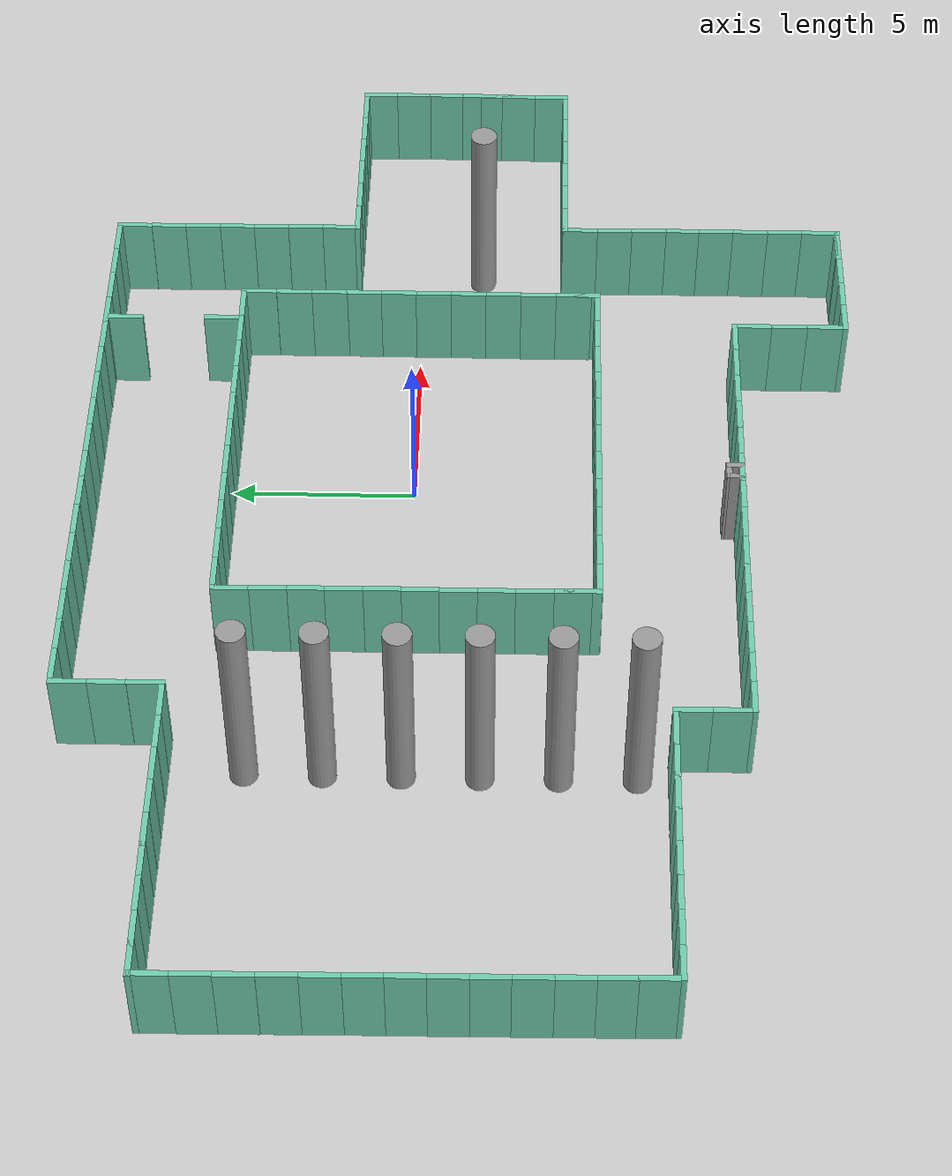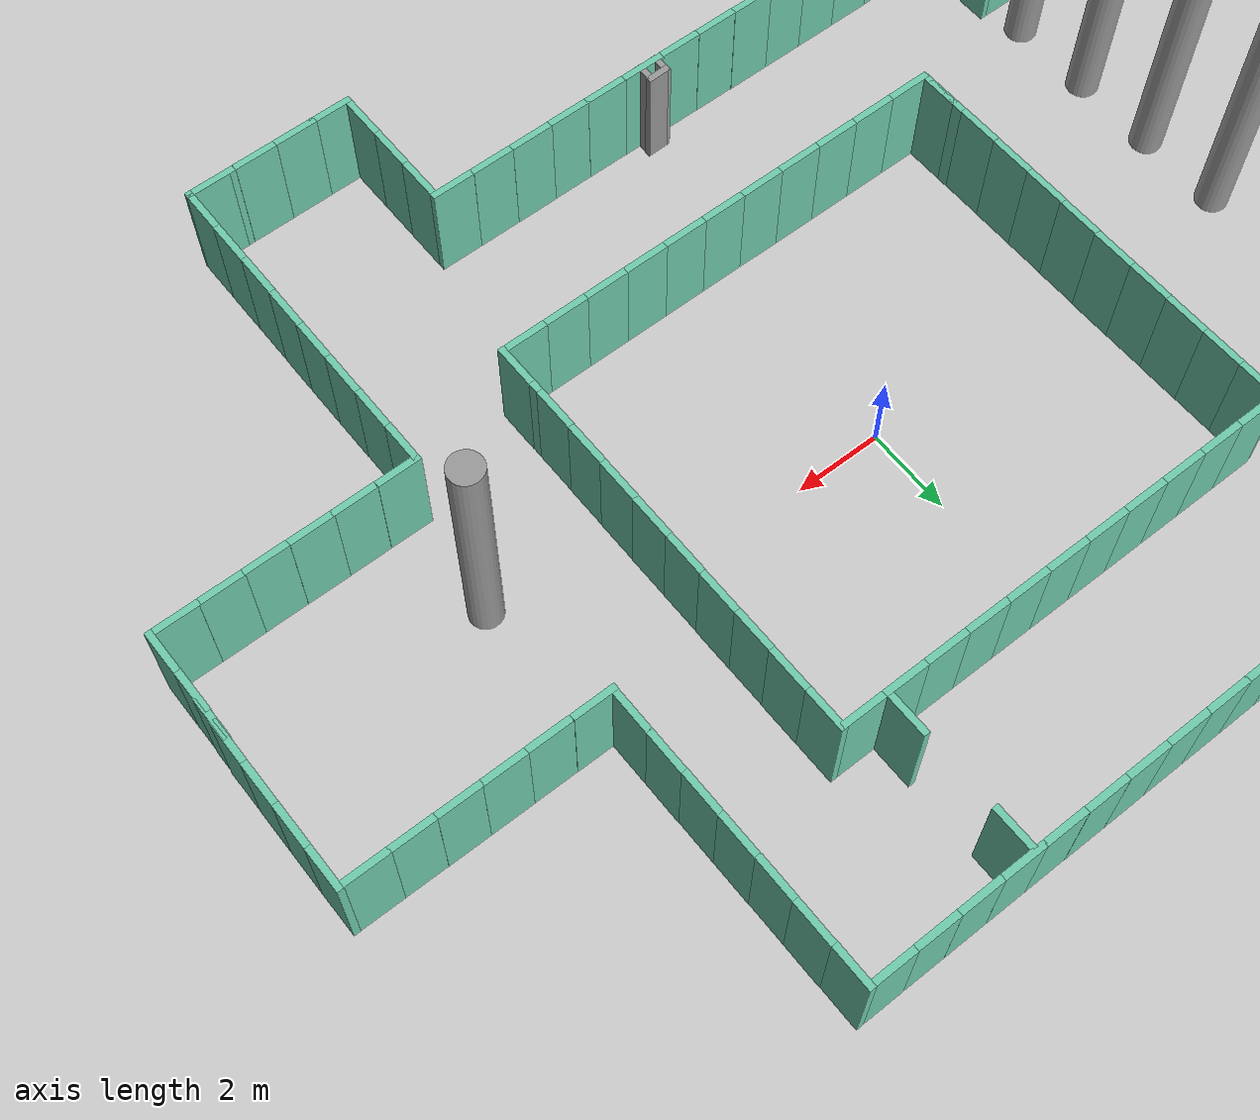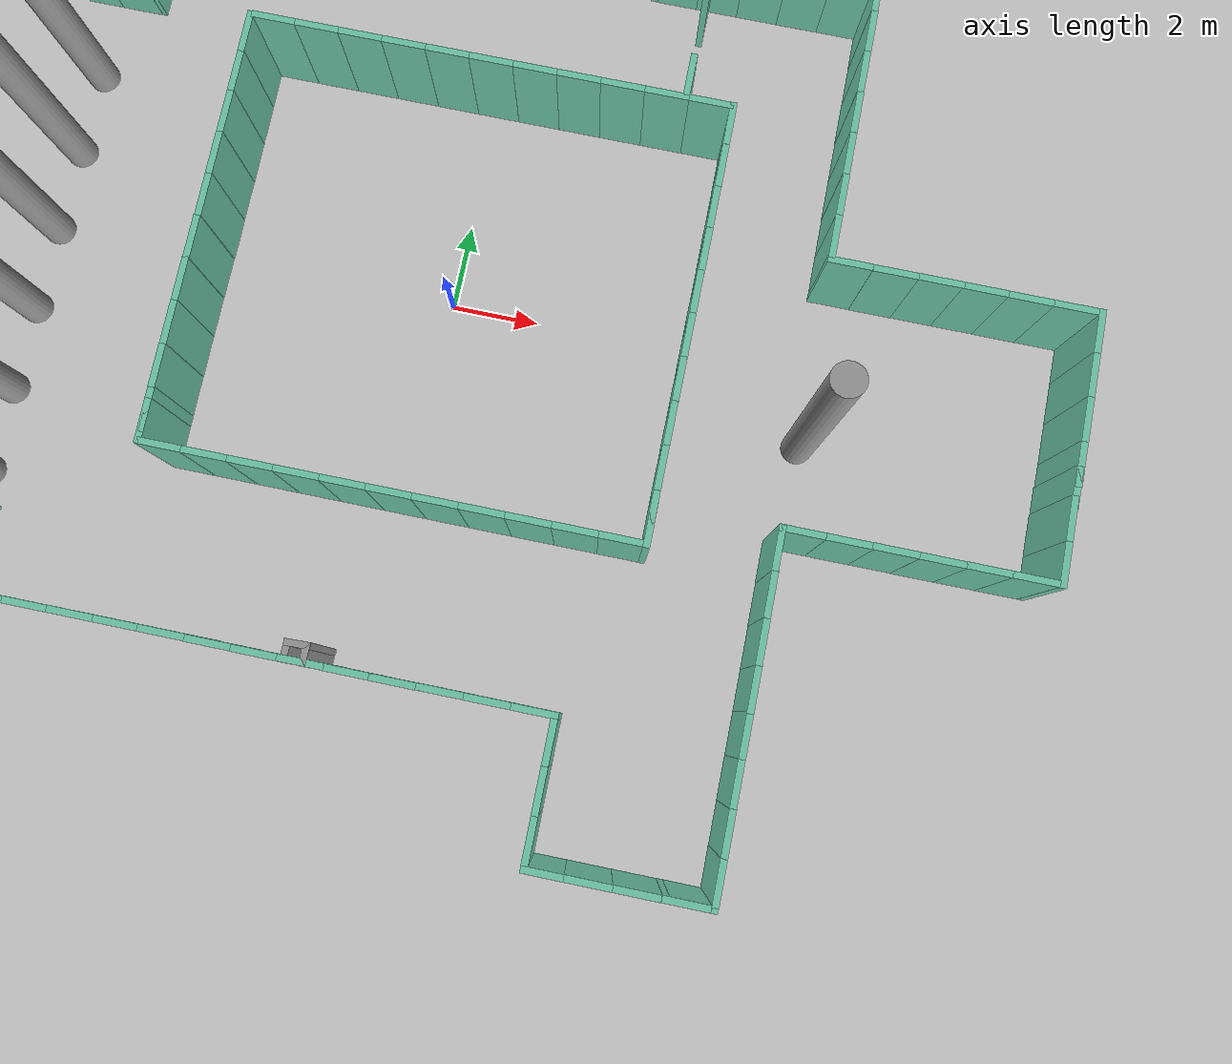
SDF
<sdf version="1.6">
 <world name="default">
  <light name="sun" type="directional">
   <pose>0 0 10 0 -0 0</pose>
   <diffuse>0.8 0.8 0.8 1</diffuse>
   <specular>0.2 0.2 0.2 1</specular>
   <attenuation>
    <range>1000</range>
    <constant>0.9</constant>
    <linear>0.01</linear>
    <quadratic>0.001</quadratic>
   </attenuation>
   <direction>-0.5 0.1 -0.9</direction>
  </light>
  <model name="ground_plane">
   <static>1</static>
   <link name="link">
    <collision name="collision">
     <geometry><plane><normal>0 0 1</normal><size>100 100</size></plane></geometry>
     <surface><friction><ode><mu>100</mu><mu2>50</mu2></ode></friction></surface>
    </collision>
    <visual name="visual">
     <cast_shadows>0</cast_shadows>
     <geometry><plane><normal>0 0 1</normal><size>100 100</size></plane></geometry>
     <material>
      <script><uri>file://media/materials/scripts/gazebo.material</uri><name>Gazebo/Grey</name></script>
     </material>
    </visual>
   </link>
  </model>
  <gravity>0 0 -9.8</gravity>
  <magnetic_field>6e-06 2.3e-05 -4.2e-05</magnetic_field>
  <atmosphere type="adiabatic"/>
  <physics name="default_physics" default="0" type="ode">
   <max_step_size>0.001</max_step_size>
   <real_time_factor>1</real_time_factor>
   <real_time_update_rate>1000</real_time_update_rate>
  </physics>
  <scene><ambient>0.4 0.4 0.4 1</ambient><background>0.7 0.7 0.7 1</background><shadows>1</shadows></scene>
  <audio><device>default</device></audio>
  <spherical_coordinates>
   <surface_model>EARTH_WGS84</surface_model>
   <latitude_deg>0</latitude_deg>
   <longitude_deg>0</longitude_deg>
   <elevation>0</elevation>
   <heading_deg>0</heading_deg>
  </spherical_coordinates>
  <model name="wall1m_0">
   <pose>5 -5 0 0 -0 0</pose>
   <link name="Wall_2">
    <collision name="Wall_2_Collision">
     <geometry><box><size>1 0.15 2.5</size></box></geometry>
     <pose>0 0 1.25 0 -0 0</pose>
    </collision>
    <visual name="Wall_2_Visual">
     <pose>0 0 1.25 0 -0 0</pose>
     <geometry><box><size>1 0.15 2.5</size></box></geometry>
     <material>
      <script><uri>file://media/materials/scripts/gazebo.material</uri><name>Gazebo/Grey</name></script>
      <ambient>0.435294 0.796078 0.67451 1</ambient>
     </material>
     <meta><layer>0</layer></meta>
    </visual>
   </link>
   <static>1</static>
  </model>
  <model name="wall1m_0_clone">
   <pose>-2 -5 0 0 -0 0</pose>
   <link name="Wall_2">
    <collision name="Wall_2_Collision">
     <geometry><box><size>1 0.15 2.5</size></box></geometry>
     <pose>0 0 1.25 0 -0 0</pose>
    </collision>
    <visual name="Wall_2_Visual">
     <pose>0 0 1.25 0 -0 0</pose>
     <geometry><box><size>1 0.15 2.5</size></box></geometry>
     <material>
      <script><uri>file://media/materials/scripts/gazebo.material</uri><name>Gazebo/Grey</name></script>
      <ambient>0.435294 0.796078 0.67451 1</ambient>
     </material>
     <meta><layer>0</layer></meta>
    </visual>
   </link>
   <static>1</static>
  </model>
  <model name="wall1m_0_clone_0">
   <pose>-1 -5 0 0 -0 0</pose>
   <link name="Wall_2">
    <collision name="Wall_2_Collision">
     <geometry><box><size>1 0.15 2.5</size></box></geometry>
     <pose>0 0 1.25 0 -0 0</pose>
    </collision>
    <visual name="Wall_2_Visual">
     <pose>0 0 1.25 0 -0 0</pose>
     <geometry><box><size>1 0.15 2.5</size></box></geometry>
     <material>
      <script><uri>file://media/materials/scripts/gazebo.material</uri><name>Gazebo/Grey</name></script>
      <ambient>0.435294 0.796078 0.67451 1</ambient>
     </material>
     <meta><layer>0</layer></meta>
    </visual>
   </link>
   <static>1</static>
  </model>
  <model name="wall1m_0_clone_1">
   <pose>0 -5 0 0 -0 0</pose>
   <link name="Wall_2">
    <collision name="Wall_2_Collision">
     <geometry><box><size>1 0.15 2.5</size></box></geometry>
     <pose>0 0 1.25 0 -0 0</pose>
    </collision>
    <visual name="Wall_2_Visual">
     <pose>0 0 1.25 0 -0 0</pose>
     <geometry><box><size>1 0.15 2.5</size></box></geometry>
     <material>
      <script><uri>file://media/materials/scripts/gazebo.material</uri><name>Gazebo/Grey</name></script>
      <ambient>0.435294 0.796078 0.67451 1</ambient>
     </material>
     <meta><layer>0</layer></meta>
    </visual>
   </link>
   <static>1</static>
  </model>
  <model name="wall1m_0_clone_2">
   <pose>1 -5 0 0 -0 0</pose>
   <link name="Wall_2">
    <collision name="Wall_2_Collision">
     <geometry><box><size>1 0.15 2.5</size></box></geometry>
     <pose>0 0 1.25 0 -0 0</pose>
    </collision>
    <visual name="Wall_2_Visual">
     <pose>0 0 1.25 0 -0 0</pose>
     <geometry><box><size>1 0.15 2.5</size></box></geometry>
     <material>
      <script><uri>file://media/materials/scripts/gazebo.material</uri><name>Gazebo/Grey</name></script>
      <ambient>0.435294 0.796078 0.67451 1</ambient>
     </material>
     <meta><layer>0</layer></meta>
    </visual>
   </link>
   <static>1</static>
  </model>
  <model name="wall1m_0_clone_3">
   <pose>2 -5 0 0 -0 0</pose>
   <link name="Wall_2">
    <collision name="Wall_2_Collision">
     <geometry><box><size>1 0.15 2.5</size></box></geometry>
     <pose>0 0 1.25 0 -0 0</pose>
    </collision>
    <visual name="Wall_2_Visual">
     <pose>0 0 1.25 0 -0 0</pose>
     <geometry><box><size>1 0.15 2.5</size></box></geometry>
     <material>
      <script><uri>file://media/materials/scripts/gazebo.material</uri><name>Gazebo/Grey</name></script>
      <ambient>0.435294 0.796078 0.67451 1</ambient>
     </material>
     <meta><layer>0</layer></meta>
    </visual>
   </link>
   <static>1</static>
  </model>
  <model name="wall1m_0_clone_4">
   <pose>3 -5 0 0 -0 0</pose>
   <link name="Wall_2">
    <collision name="Wall_2_Collision">
     <geometry><box><size>1 0.15 2.5</size></box></geometry>
     <pose>0 0 1.25 0 -0 0</pose>
    </collision>
    <visual name="Wall_2_Visual">
     <pose>0 0 1.25 0 -0 0</pose>
     <geometry><box><size>1 0.15 2.5</size></box></geometry>
     <material>
      <script><uri>file://media/materials/scripts/gazebo.material</uri><name>Gazebo/Grey</name></script>
      <ambient>0.435294 0.796078 0.67451 1</ambient>
     </material>
     <meta><layer>0</layer></meta>
    </visual>
   </link>
   <static>1</static>
  </model>
  <model name="wall1m_0_clone_5">
   <pose>4 -5 0 0 -0 0</pose>
   <link name="Wall_2">
    <collision name="Wall_2_Collision">
     <geometry><box><size>1 0.15 2.5</size></box></geometry>
     <pose>0 0 1.25 0 -0 0</pose>
    </collision>
    <visual name="Wall_2_Visual">
     <pose>0 0 1.25 0 -0 0</pose>
     <geometry><box><size>1 0.15 2.5</size></box></geometry>
     <material>
      <script><uri>file://media/materials/scripts/gazebo.material</uri><name>Gazebo/Grey</name></script>
      <ambient>0.435294 0.796078 0.67451 1</ambient>
     </material>
     <meta><layer>0</layer></meta>
    </visual>
   </link>
   <static>1</static>
  </model>
  <model name="wall1m_0_clone_6">
   <pose>-3 -5 0 0 -0 0</pose>
   <link name="Wall_2">
    <collision name="Wall_2_Collision">
     <geometry><box><size>1 0.15 2.5</size></box></geometry>
     <pose>0 0 1.25 0 -0 0</pose>
    </collision>
    <visual name="Wall_2_Visual">
     <pose>0 0 1.25 0 -0 0</pose>
     <geometry><box><size>1 0.15 2.5</size></box></geometry>
     <material>
      <script><uri>file://media/materials/scripts/gazebo.material</uri><name>Gazebo/Grey</name></script>
      <ambient>0.435294 0.796078 0.67451 1</ambient>
     </material>
     <meta><layer>0</layer></meta>
    </visual>
   </link>
   <static>1</static>
  </model>
  <model name="wall1m_0_clone_7">
   <pose>-4 -5 0 0 -0 0</pose>
   <link name="Wall_2">
    <collision name="Wall_2_Collision">
     <geometry><box><size>1 0.15 2.5</size></box></geometry>
     <pose>0 0 1.25 0 -0 0</pose>
    </collision>
    <visual name="Wall_2_Visual">
     <pose>0 0 1.25 0 -0 0</pose>
     <geometry><box><size>1 0.15 2.5</size></box></geometry>
     <material>
      <script><uri>file://media/materials/scripts/gazebo.material</uri><name>Gazebo/Grey</name></script>
      <ambient>0.435294 0.796078 0.67451 1</ambient>
     </material>
     <meta><layer>0</layer></meta>
    </visual>
   </link>
   <static>1</static>
  </model>
  <model name="wall1m_0_clone_8">
   <pose>-5 -5 0 0 -0 0</pose>
   <link name="Wall_2">
    <collision name="Wall_2_Collision">
     <geometry><box><size>1 0.15 2.5</size></box></geometry>
     <pose>0 0 1.25 0 -0 0</pose>
    </collision>
    <visual name="Wall_2_Visual">
     <pose>0 0 1.25 0 -0 0</pose>
     <geometry><box><size>1 0.15 2.5</size></box></geometry>
     <material>
      <script><uri>file://media/materials/scripts/gazebo.material</uri><name>Gazebo/Grey</name></script>
      <ambient>0.435294 0.796078 0.67451 1</ambient>
     </material>
     <meta><layer>0</layer></meta>
    </visual>
   </link>
   <static>1</static>
  </model>
  <model name="wall1m_0_clone_8_clone">
   <pose>-5 5 0 0 -0 0</pose>
   <link name="Wall_2">
    <collision name="Wall_2_Collision">
     <geometry><box><size>1 0.15 2.5</size></box></geometry>
     <pose>0 0 1.25 0 -0 0</pose>
    </collision>
    <visual name="Wall_2_Visual">
     <pose>0 0 1.25 0 -0 0</pose>
     <geometry><box><size>1 0.15 2.5</size></box></geometry>
     <material>
      <script><uri>file://media/materials/scripts/gazebo.material</uri><name>Gazebo/Grey</name></script>
      <ambient>0.435294 0.796078 0.67451 1</ambient>
     </material>
     <meta><layer>0</layer></meta>
    </visual>
   </link>
   <static>1</static>
  </model>
  <model name="wall1m_0_clone_8_clone_0">
   <pose>-4 5 0 0 -0 0</pose>
   <link name="Wall_2">
    <collision name="Wall_2_Collision">
     <geometry><box><size>1 0.15 2.5</size></box></geometry>
     <pose>0 0 1.25 0 -0 0</pose>
    </collision>
    <visual name="Wall_2_Visual">
     <pose>0 0 1.25 0 -0 0</pose>
     <geometry><box><size>1 0.15 2.5</size></box></geometry>
     <material>
      <script><uri>file://media/materials/scripts/gazebo.material</uri><name>Gazebo/Grey</name></script>
      <ambient>0.435294 0.796078 0.67451 1</ambient>
     </material>
     <meta><layer>0</layer></meta>
    </visual>
   </link>
   <static>1</static>
  </model>
  <model name="wall1m_0_clone_8_clone_1">
   <pose>-3 5 0 0 -0 0</pose>
   <link name="Wall_2">
    <collision name="Wall_2_Collision">
     <geometry><box><size>1 0.15 2.5</size></box></geometry>
     <pose>0 0 1.25 0 -0 0</pose>
    </collision>
    <visual name="Wall_2_Visual">
     <pose>0 0 1.25 0 -0 0</pose>
     <geometry><box><size>1 0.15 2.5</size></box></geometry>
     <material>
      <script><uri>file://media/materials/scripts/gazebo.material</uri><name>Gazebo/Grey</name></script>
      <ambient>0.435294 0.796078 0.67451 1</ambient>
     </material>
     <meta><layer>0</layer></meta>
    </visual>
   </link>
   <static>1</static>
  </model>
  <model name="wall1m_0_clone_8_clone_2">
   <pose>-2 5 0 0 -0 0</pose>
   <link name="Wall_2">
    <collision name="Wall_2_Collision">
     <geometry><box><size>1 0.15 2.5</size></box></geometry>
     <pose>0 0 1.25 0 -0 0</pose>
    </collision>
    <visual name="Wall_2_Visual">
     <pose>0 0 1.25 0 -0 0</pose>
     <geometry><box><size>1 0.15 2.5</size></box></geometry>
     <material>
      <script><uri>file://media/materials/scripts/gazebo.material</uri><name>Gazebo/Grey</name></script>
      <ambient>0.435294 0.796078 0.67451 1</ambient>
     </material>
     <meta><layer>0</layer></meta>
    </visual>
   </link>
   <static>1</static>
  </model>
  <model name="wall1m_0_clone_8_clone_3">
   <pose>-1 5 0 0 -0 0</pose>
   <link name="Wall_2">
    <collision name="Wall_2_Collision">
     <geometry><box><size>1 0.15 2.5</size></box></geometry>
     <pose>0 0 1.25 0 -0 0</pose>
    </collision>
    <visual name="Wall_2_Visual">
     <pose>0 0 1.25 0 -0 0</pose>
     <geometry><box><size>1 0.15 2.5</size></box></geometry>
     <material>
      <script><uri>file://media/materials/scripts/gazebo.material</uri><name>Gazebo/Grey</name></script>
      <ambient>0.435294 0.796078 0.67451 1</ambient>
     </material>
     <meta><layer>0</layer></meta>
    </visual>
   </link>
   <static>1</static>
  </model>
  <model name="wall1m_0_clone_8_clone_4">
   <pose>0 5 0 0 -0 0</pose>
   <link name="Wall_2">
    <collision name="Wall_2_Collision">
     <geometry><box><size>1 0.15 2.5</size></box></geometry>
     <pose>0 0 1.25 0 -0 0</pose>
    </collision>
    <visual name="Wall_2_Visual">
     <pose>0 0 1.25 0 -0 0</pose>
     <geometry><box><size>1 0.15 2.5</size></box></geometry>
     <material>
      <script><uri>file://media/materials/scripts/gazebo.material</uri><name>Gazebo/Grey</name></script>
      <ambient>0.435294 0.796078 0.67451 1</ambient>
     </material>
     <meta><layer>0</layer></meta>
    </visual>
   </link>
   <static>1</static>
  </model>
  <model name="wall1m_0_clone_8_clone_5">
   <pose>1 5 0 0 -0 0</pose>
   <link name="Wall_2">
    <collision name="Wall_2_Collision">
     <geometry><box><size>1 0.15 2.5</size></box></geometry>
     <pose>0 0 1.25 0 -0 0</pose>
    </collision>
    <visual name="Wall_2_Visual">
     <pose>0 0 1.25 0 -0 0</pose>
     <geometry><box><size>1 0.15 2.5</size></box></geometry>
     <material>
      <script><uri>file://media/materials/scripts/gazebo.material</uri><name>Gazebo/Grey</name></script>
      <ambient>0.435294 0.796078 0.67451 1</ambient>
     </material>
     <meta><layer>0</layer></meta>
    </visual>
   </link>
   <static>1</static>
  </model>
  <model name="wall1m_0_clone_8_clone_6">
   <pose>2 5 0 0 -0 0</pose>
   <link name="Wall_2">
    <collision name="Wall_2_Collision">
     <geometry><box><size>1 0.15 2.5</size></box></geometry>
     <pose>0 0 1.25 0 -0 0</pose>
    </collision>
    <visual name="Wall_2_Visual">
     <pose>0 0 1.25 0 -0 0</pose>
     <geometry><box><size>1 0.15 2.5</size></box></geometry>
     <material>
      <script><uri>file://media/materials/scripts/gazebo.material</uri><name>Gazebo/Grey</name></script>
      <ambient>0.435294 0.796078 0.67451 1</ambient>
     </material>
     <meta><layer>0</layer></meta>
    </visual>
   </link>
   <static>1</static>
  </model>
  <model name="wall1m_0_clone_8_clone_7">
   <pose>3 5 0 0 -0 0</pose>
   <link name="Wall_2">
    <collision name="Wall_2_Collision">
     <geometry><box><size>1 0.15 2.5</size></box></geometry>
     <pose>0 0 1.25 0 -0 0</pose>
    </collision>
    <visual name="Wall_2_Visual">
     <pose>0 0 1.25 0 -0 0</pose>
     <geometry><box><size>1 0.15 2.5</size></box></geometry>
     <material>
      <script><uri>file://media/materials/scripts/gazebo.material</uri><name>Gazebo/Grey</name></script>
      <ambient>0.435294 0.796078 0.67451 1</ambient>
     </material>
     <meta><layer>0</layer></meta>
    </visual>
   </link>
   <static>1</static>
  </model>
  <model name="wall1m_0_clone_8_clone_8">
   <pose>4 5 0 0 -0 0</pose>
   <link name="Wall_2">
    <collision name="Wall_2_Collision">
     <geometry><box><size>1 0.15 2.5</size></box></geometry>
     <pose>0 0 1.25 0 -0 0</pose>
    </collision>
    <visual name="Wall_2_Visual">
     <pose>0 0 1.25 0 -0 0</pose>
     <geometry><box><size>1 0.15 2.5</size></box></geometry>
     <material>
      <script><uri>file://media/materials/scripts/gazebo.material</uri><name>Gazebo/Grey</name></script>
      <ambient>0.435294 0.796078 0.67451 1</ambient>
     </material>
     <meta><layer>0</layer></meta>
    </visual>
   </link>
   <static>1</static>
  </model>
  <model name="wall1m_0_clone_8_clone_9">
   <pose>5 5 0 0 -0 0</pose>
   <link name="Wall_2">
    <collision name="Wall_2_Collision">
     <geometry><box><size>1 0.15 2.5</size></box></geometry>
     <pose>0 0 1.25 0 -0 0</pose>
    </collision>
    <visual name="Wall_2_Visual">
     <pose>0 0 1.25 0 -0 0</pose>
     <geometry><box><size>1 0.15 2.5</size></box></geometry>
     <material>
      <script><uri>file://media/materials/scripts/gazebo.material</uri><name>Gazebo/Grey</name></script>
      <ambient>0.435294 0.796078 0.67451 1</ambient>
     </material>
     <meta><layer>0</layer></meta>
    </visual>
   </link>
   <static>1</static>
  </model>
  <model name="wall1m_0_clone_8_clone_9_clone">
   <pose>5.49961 4.57845 0 0 0 -1.5658</pose>
   <link name="Wall_2">
    <collision name="Wall_2_Collision">
     <geometry><box><size>1 0.15 2.5</size></box></geometry>
     <pose>0 0 1.25 0 -0 0</pose>
    </collision>
    <visual name="Wall_2_Visual">
     <pose>0 0 1.25 0 -0 0</pose>
     <geometry><box><size>1 0.15 2.5</size></box></geometry>
     <material>
      <script><uri>file://media/materials/scripts/gazebo.material</uri><name>Gazebo/Grey</name></script>
      <ambient>0.435294 0.796078 0.67451 1</ambient>
     </material>
     <meta><layer>0</layer></meta>
    </visual>
   </link>
   <static>1</static>
  </model>
  <model name="wall1m_0_clone_8_clone_9_clone_clone_11">
   <pose>-5.50391 3.57304 0 0 0 -1.56</pose>
   <link name="Wall_2">
    <collision name="Wall_2_Collision">
     <geometry><box><size>1 0.15 2.5</size></box></geometry>
     <pose>0 0 1.25 0 -0 0</pose>
    </collision>
    <visual name="Wall_2_Visual">
     <pose>0 0 1.25 0 -0 0</pose>
     <geometry><box><size>1 0.15 2.5</size></box></geometry>
     <material>
      <script><uri>file://media/materials/scripts/gazebo.material</uri><name>Gazebo/Grey</name></script>
      <ambient>0.435294 0.796078 0.67451 1</ambient>
     </material>
     <meta><layer>0</layer></meta>
    </visual>
   </link>
   <static>1</static>
  </model>
  <model name="wall1m_0_clone_8_clone_9_clone_clone_12">
   <pose>-5.49192 2.60858 0 0 0 -1.56</pose>
   <link name="Wall_2">
    <collision name="Wall_2_Collision">
     <geometry><box><size>1 0.15 2.5</size></box></geometry>
     <pose>0 0 1.25 0 -0 0</pose>
    </collision>
    <visual name="Wall_2_Visual">
     <pose>0 0 1.25 0 -0 0</pose>
     <geometry><box><size>1 0.15 2.5</size></box></geometry>
     <material>
      <script><uri>file://media/materials/scripts/gazebo.material</uri><name>Gazebo/Grey</name></script>
      <ambient>0.435294 0.796078 0.67451 1</ambient>
     </material>
     <meta><layer>0</layer></meta>
    </visual>
   </link>
   <static>1</static>
  </model>
  <model name="wall1m_0_clone_8_clone_9_clone_clone_13">
   <pose>-5.48641 1.61058 0 0 0 -1.56</pose>
   <link name="Wall_2">
    <collision name="Wall_2_Collision">
     <geometry><box><size>1 0.15 2.5</size></box></geometry>
     <pose>0 0 1.25 0 -0 0</pose>
    </collision>
    <visual name="Wall_2_Visual">
     <pose>0 0 1.25 0 -0 0</pose>
     <geometry><box><size>1 0.15 2.5</size></box></geometry>
     <material>
      <script><uri>file://media/materials/scripts/gazebo.material</uri><name>Gazebo/Grey</name></script>
      <ambient>0.435294 0.796078 0.67451 1</ambient>
     </material>
     <meta><layer>0</layer></meta>
    </visual>
   </link>
   <static>1</static>
  </model>
  <model name="wall1m_0_clone_8_clone_9_clone_clone_14">
   <pose>-5.47454 0.61865 0 0 0 -1.56</pose>
   <link name="Wall_2">
    <collision name="Wall_2_Collision">
     <geometry><box><size>1 0.15 2.5</size></box></geometry>
     <pose>0 0 1.25 0 -0 0</pose>
    </collision>
    <visual name="Wall_2_Visual">
     <pose>0 0 1.25 0 -0 0</pose>
     <geometry><box><size>1 0.15 2.5</size></box></geometry>
     <material>
      <script><uri>file://media/materials/scripts/gazebo.material</uri><name>Gazebo/Grey</name></script>
      <ambient>0.435294 0.796078 0.67451 1</ambient>
     </material>
     <meta><layer>0</layer></meta>
    </visual>
   </link>
   <static>1</static>
  </model>
  <model name="wall1m_0_clone_8_clone_9_clone_clone_15">
   <pose>-5.47664 -0.377289 0 0 0 -1.56</pose>
   <link name="Wall_2">
    <collision name="Wall_2_Collision">
     <geometry><box><size>1 0.15 2.5</size></box></geometry>
     <pose>0 0 1.25 0 -0 0</pose>
    </collision>
    <visual name="Wall_2_Visual">
     <pose>0 0 1.25 0 -0 0</pose>
     <geometry><box><size>1 0.15 2.5</size></box></geometry>
     <material>
      <script><uri>file://media/materials/scripts/gazebo.material</uri><name>Gazebo/Grey</name></script>
      <ambient>0.435294 0.796078 0.67451 1</ambient>
     </material>
     <meta><layer>0</layer></meta>
    </visual>
   </link>
   <static>1</static>
  </model>
  <model name="wall1m_0_clone_8_clone_9_clone_clone_16">
   <pose>-5.47622 -1.34647 0 0 0 -1.56</pose>
   <link name="Wall_2">
    <collision name="Wall_2_Collision">
     <geometry><box><size>1 0.15 2.5</size></box></geometry>
     <pose>0 0 1.25 0 -0 0</pose>
    </collision>
    <visual name="Wall_2_Visual">
     <pose>0 0 1.25 0 -0 0</pose>
     <geometry><box><size>1 0.15 2.5</size></box></geometry>
     <material>
      <script><uri>file://media/materials/scripts/gazebo.material</uri><name>Gazebo/Grey</name></script>
      <ambient>0.435294 0.796078 0.67451 1</ambient>
     </material>
     <meta><layer>0</layer></meta>
    </visual>
   </link>
   <static>1</static>
  </model>
  <model name="wall1m_0_clone_8_clone_9_clone_clone_17">
   <pose>-5.46878 -2.34019 0 0 0 -1.56</pose>
   <link name="Wall_2">
    <collision name="Wall_2_Collision">
     <geometry><box><size>1 0.15 2.5</size></box></geometry>
     <pose>0 0 1.25 0 -0 0</pose>
    </collision>
    <visual name="Wall_2_Visual">
     <pose>0 0 1.25 0 -0 0</pose>
     <geometry><box><size>1 0.15 2.5</size></box></geometry>
     <material>
      <script><uri>file://media/materials/scripts/gazebo.material</uri><name>Gazebo/Grey</name></script>
      <ambient>0.435294 0.796078 0.67451 1</ambient>
     </material>
     <meta><layer>0</layer></meta>
    </visual>
   </link>
   <static>1</static>
  </model>
  <model name="wall1m_0_clone_8_clone_9_clone_clone_18">
   <pose>-5.46314 -3.32192 0 0 0 -1.56</pose>
   <link name="Wall_2">
    <collision name="Wall_2_Collision">
     <geometry><box><size>1 0.15 2.5</size></box></geometry>
     <pose>0 0 1.25 0 -0 0</pose>
    </collision>
    <visual name="Wall_2_Visual">
     <pose>0 0 1.25 0 -0 0</pose>
     <geometry><box><size>1 0.15 2.5</size></box></geometry>
     <material>
      <script><uri>file://media/materials/scripts/gazebo.material</uri><name>Gazebo/Grey</name></script>
      <ambient>0.435294 0.796078 0.67451 1</ambient>
     </material>
     <meta><layer>0</layer></meta>
    </visual>
   </link>
   <static>1</static>
  </model>
  <model name="wall1m_0_clone_8_clone_9_clone_clone_19">
   <pose>-5.44807 -4.30765 0 0 0 -1.56</pose>
   <link name="Wall_2">
    <collision name="Wall_2_Collision">
     <geometry><box><size>1 0.15 2.5</size></box></geometry>
     <pose>0 0 1.25 0 -0 0</pose>
    </collision>
    <visual name="Wall_2_Visual">
     <pose>0 0 1.25 0 -0 0</pose>
     <geometry><box><size>1 0.15 2.5</size></box></geometry>
     <material>
      <script><uri>file://media/materials/scripts/gazebo.material</uri><name>Gazebo/Grey</name></script>
      <ambient>0.435294 0.796078 0.67451 1</ambient>
     </material>
     <meta><layer>0</layer></meta>
    </visual>
   </link>
   <static>1</static>
  </model>
  <model name="wall1m_0_clone_8_clone_9_clone_clone_20">
   <pose>-5.44478 -4.56506 0 0 0 -1.56</pose>
   <link name="Wall_2">
    <collision name="Wall_2_Collision">
     <geometry><box><size>1 0.15 2.5</size></box></geometry>
     <pose>0 0 1.25 0 -0 0</pose>
    </collision>
    <visual name="Wall_2_Visual">
     <pose>0 0 1.25 0 -0 0</pose>
     <geometry><box><size>1 0.15 2.5</size></box></geometry>
     <material>
      <script><uri>file://media/materials/scripts/gazebo.material</uri><name>Gazebo/Grey</name></script>
      <ambient>0.435294 0.796078 0.67451 1</ambient>
     </material>
     <meta><layer>0</layer></meta>
    </visual>
   </link>
   <static>1</static>
  </model>
  <model name="wall1m_0_clone_8_clone_9_clone_clone_26">
   <pose>-8.67069 6.41348 0 0 0 -1.5658</pose>
   <link name="Wall_2">
    <collision name="Wall_2_Collision">
     <geometry><box><size>1 0.15 2.5</size></box></geometry>
     <pose>0 0 1.25 0 -0 0</pose>
    </collision>
    <visual name="Wall_2_Visual">
     <pose>0 0 1.25 0 -0 0</pose>
     <geometry><box><size>1 0.15 2.5</size></box></geometry>
     <material>
      <script><uri>file://media/materials/scripts/gazebo.material</uri><name>Gazebo/Grey</name></script>
      <ambient>0.435294 0.796078 0.67451 1</ambient>
     </material>
     <meta><layer>0</layer></meta>
    </visual>
   </link>
   <static>1</static>
  </model>
  <model name="wall1m_0_clone_8_clone_9_clone_clone_27">
   <pose>-8.68063 7.3869 0 0 0 -1.5658</pose>
   <link name="Wall_2">
    <collision name="Wall_2_Collision">
     <geometry><box><size>1 0.15 2.5</size></box></geometry>
     <pose>0 0 1.25 0 -0 0</pose>
    </collision>
    <visual name="Wall_2_Visual">
     <pose>0 0 1.25 0 -0 0</pose>
     <geometry><box><size>1 0.15 2.5</size></box></geometry>
     <material>
      <script><uri>file://media/materials/scripts/gazebo.material</uri><name>Gazebo/Grey</name></script>
      <ambient>0.435294 0.796078 0.67451 1</ambient>
     </material>
     <meta><layer>0</layer></meta>
    </visual>
   </link>
   <static>1</static>
  </model>
  <model name="wall1m_0_clone_8_clone_9_clone_clone_28">
   <pose>-8.68183 8.38093 0 0 0 -1.5658</pose>
   <link name="Wall_2">
    <collision name="Wall_2_Collision">
     <geometry><box><size>1 0.15 2.5</size></box></geometry>
     <pose>0 0 1.25 0 -0 0</pose>
    </collision>
    <visual name="Wall_2_Visual">
     <pose>0 0 1.25 0 -0 0</pose>
     <geometry><box><size>1 0.15 2.5</size></box></geometry>
     <material>
      <script><uri>file://media/materials/scripts/gazebo.material</uri><name>Gazebo/Grey</name></script>
      <ambient>0.435294 0.796078 0.67451 1</ambient>
     </material>
     <meta><layer>0</layer></meta>
    </visual>
   </link>
   <static>1</static>
  </model>
  <model name="wall1m_0_clone_8_clone_clone">
   <pose>-8.1226 8.81472 0 0 -0 0</pose>
   <link name="Wall_2">
    <collision name="Wall_2_Collision">
     <geometry><box><size>1 0.15 2.5</size></box></geometry>
     <pose>0 0 1.25 0 -0 0</pose>
    </collision>
    <visual name="Wall_2_Visual">
     <pose>0 0 1.25 0 -0 0</pose>
     <geometry><box><size>1 0.15 2.5</size></box></geometry>
     <material>
      <script><uri>file://media/materials/scripts/gazebo.material</uri><name>Gazebo/Grey</name></script>
      <ambient>0.435294 0.796078 0.67451 1</ambient>
     </material>
     <meta><layer>0</layer></meta>
    </visual>
   </link>
   <static>1</static>
  </model>
  <model name="wall1m_0_clone_8_clone_clone_0">
   <pose>-7.14062 8.80997 0 0 -0 0</pose>
   <link name="Wall_2">
    <collision name="Wall_2_Collision">
     <geometry><box><size>1 0.15 2.5</size></box></geometry>
     <pose>0 0 1.25 0 -0 0</pose>
    </collision>
    <visual name="Wall_2_Visual">
     <pose>0 0 1.25 0 -0 0</pose>
     <geometry><box><size>1 0.15 2.5</size></box></geometry>
     <material>
      <script><uri>file://media/materials/scripts/gazebo.material</uri><name>Gazebo/Grey</name></script>
      <ambient>0.435294 0.796078 0.67451 1</ambient>
     </material>
     <meta><layer>0</layer></meta>
    </visual>
   </link>
   <static>1</static>
  </model>
  <model name="wall1m_0_clone_8_clone_clone_1">
   <pose>-6.17103 8.8091 0 0 -0 0</pose>
   <link name="Wall_2">
    <collision name="Wall_2_Collision">
     <geometry><box><size>1 0.15 2.5</size></box></geometry>
     <pose>0 0 1.25 0 -0 0</pose>
    </collision>
    <visual name="Wall_2_Visual">
     <pose>0 0 1.25 0 -0 0</pose>
     <geometry><box><size>1 0.15 2.5</size></box></geometry>
     <material>
      <script><uri>file://media/materials/scripts/gazebo.material</uri><name>Gazebo/Grey</name></script>
      <ambient>0.435294 0.796078 0.67451 1</ambient>
     </material>
     <meta><layer>0</layer></meta>
    </visual>
   </link>
   <static>1</static>
  </model>
  <model name="wall1m_0_clone_8_clone_clone_2">
   <pose>-5.18883 8.81035 0 0 -0 0</pose>
   <link name="Wall_2">
    <collision name="Wall_2_Collision">
     <geometry><box><size>1 0.15 2.5</size></box></geometry>
     <pose>0 0 1.25 0 -0 0</pose>
    </collision>
    <visual name="Wall_2_Visual">
     <pose>0 0 1.25 0 -0 0</pose>
     <geometry><box><size>1 0.15 2.5</size></box></geometry>
     <material>
      <script><uri>file://media/materials/scripts/gazebo.material</uri><name>Gazebo/Grey</name></script>
      <ambient>0.435294 0.796078 0.67451 1</ambient>
     </material>
     <meta><layer>0</layer></meta>
    </visual>
   </link>
   <static>1</static>
  </model>
  <model name="wall1m_0_clone_8_clone_clone_3">
   <pose>-4.21856 8.80952 0 0 -0 0</pose>
   <link name="Wall_2">
    <collision name="Wall_2_Collision">
     <geometry><box><size>1 0.15 2.5</size></box></geometry>
     <pose>0 0 1.25 0 -0 0</pose>
    </collision>
    <visual name="Wall_2_Visual">
     <pose>0 0 1.25 0 -0 0</pose>
     <geometry><box><size>1 0.15 2.5</size></box></geometry>
     <material>
      <script><uri>file://media/materials/scripts/gazebo.material</uri><name>Gazebo/Grey</name></script>
      <ambient>0.435294 0.796078 0.67451 1</ambient>
     </material>
     <meta><layer>0</layer></meta>
    </visual>
   </link>
   <static>1</static>
  </model>
  <model name="wall1m_0_clone_8_clone_clone_4">
   <pose>-3.22087 8.8088 0 0 -0 0</pose>
   <link name="Wall_2">
    <collision name="Wall_2_Collision">
     <geometry><box><size>1 0.15 2.5</size></box></geometry>
     <pose>0 0 1.25 0 -0 0</pose>
    </collision>
    <visual name="Wall_2_Visual">
     <pose>0 0 1.25 0 -0 0</pose>
     <geometry><box><size>1 0.15 2.5</size></box></geometry>
     <material>
      <script><uri>file://media/materials/scripts/gazebo.material</uri><name>Gazebo/Grey</name></script>
      <ambient>0.435294 0.796078 0.67451 1</ambient>
     </material>
     <meta><layer>0</layer></meta>
    </visual>
   </link>
   <static>1</static>
  </model>
  <model name="wall1m_0_clone_8_clone_clone_5">
   <pose>-2.23037 8.79955 0 0 -0 0</pose>
   <link name="Wall_2">
    <collision name="Wall_2_Collision">
     <geometry><box><size>1 0.15 2.5</size></box></geometry>
     <pose>0 0 1.25 0 -0 0</pose>
    </collision>
    <visual name="Wall_2_Visual">
     <pose>0 0 1.25 0 -0 0</pose>
     <geometry><box><size>1 0.15 2.5</size></box></geometry>
     <material>
      <script><uri>file://media/materials/scripts/gazebo.material</uri><name>Gazebo/Grey</name></script>
      <ambient>0.435294 0.796078 0.67451 1</ambient>
     </material>
     <meta><layer>0</layer></meta>
    </visual>
   </link>
   <static>1</static>
  </model>
  <model name="wall1m_0_clone_8_clone_clone_6">
   <pose>-1.25825 8.79936 0 0 -0 0</pose>
   <link name="Wall_2">
    <collision name="Wall_2_Collision">
     <geometry><box><size>1 0.15 2.5</size></box></geometry>
     <pose>0 0 1.25 0 -0 0</pose>
    </collision>
    <visual name="Wall_2_Visual">
     <pose>0 0 1.25 0 -0 0</pose>
     <geometry><box><size>1 0.15 2.5</size></box></geometry>
     <material>
      <script><uri>file://media/materials/scripts/gazebo.material</uri><name>Gazebo/Grey</name></script>
      <ambient>0.435294 0.796078 0.67451 1</ambient>
     </material>
     <meta><layer>0</layer></meta>
    </visual>
   </link>
   <static>1</static>
  </model>
  <model name="wall1m_0_clone_8_clone_clone_7">
   <pose>-0.28955 8.79942 0 0 -0 0</pose>
   <link name="Wall_2">
    <collision name="Wall_2_Collision">
     <geometry><box><size>1 0.15 2.5</size></box></geometry>
     <pose>0 0 1.25 0 -0 0</pose>
    </collision>
    <visual name="Wall_2_Visual">
     <pose>0 0 1.25 0 -0 0</pose>
     <geometry><box><size>1 0.15 2.5</size></box></geometry>
     <material>
      <script><uri>file://media/materials/scripts/gazebo.material</uri><name>Gazebo/Grey</name></script>
      <ambient>0.435294 0.796078 0.67451 1</ambient>
     </material>
     <meta><layer>0</layer></meta>
    </visual>
   </link>
   <static>1</static>
  </model>
  <model name="wall1m_0_clone_8_clone_clone_8">
   <pose>0.695038 8.79962 0 0 -0 0</pose>
   <link name="Wall_2">
    <collision name="Wall_2_Collision">
     <geometry><box><size>1 0.15 2.5</size></box></geometry>
     <pose>0 0 1.25 0 -0 0</pose>
    </collision>
    <visual name="Wall_2_Visual">
     <pose>0 0 1.25 0 -0 0</pose>
     <geometry><box><size>1 0.15 2.5</size></box></geometry>
     <material>
      <script><uri>file://media/materials/scripts/gazebo.material</uri><name>Gazebo/Grey</name></script>
      <ambient>0.435294 0.796078 0.67451 1</ambient>
     </material>
     <meta><layer>0</layer></meta>
    </visual>
   </link>
   <static>1</static>
  </model>
  <model name="wall1m_0_clone_8_clone_clone_9">
   <pose>1.69822 8.80194 0 0 -0 0</pose>
   <link name="Wall_2">
    <collision name="Wall_2_Collision">
     <geometry><box><size>1 0.15 2.5</size></box></geometry>
     <pose>0 0 1.25 0 -0 0</pose>
    </collision>
    <visual name="Wall_2_Visual">
     <pose>0 0 1.25 0 -0 0</pose>
     <geometry><box><size>1 0.15 2.5</size></box></geometry>
     <material>
      <script><uri>file://media/materials/scripts/gazebo.material</uri><name>Gazebo/Grey</name></script>
      <ambient>0.435294 0.796078 0.67451 1</ambient>
     </material>
     <meta><layer>0</layer></meta>
    </visual>
   </link>
   <static>1</static>
  </model>
  <model name="wall1m_0_clone_8_clone_clone_10">
   <pose>2.69303 8.80098 0 0 -0 0</pose>
   <link name="Wall_2">
    <collision name="Wall_2_Collision">
     <geometry><box><size>1 0.15 2.5</size></box></geometry>
     <pose>0 0 1.25 0 -0 0</pose>
    </collision>
    <visual name="Wall_2_Visual">
     <pose>0 0 1.25 0 -0 0</pose>
     <geometry><box><size>1 0.15 2.5</size></box></geometry>
     <material>
      <script><uri>file://media/materials/scripts/gazebo.material</uri><name>Gazebo/Grey</name></script>
      <ambient>0.435294 0.796078 0.67451 1</ambient>
     </material>
     <meta><layer>0</layer></meta>
    </visual>
   </link>
   <static>1</static>
  </model>
  <model name="wall1m_0_clone_8_clone_clone_11">
   <pose>3.69045 8.7948 0 0 -0 0</pose>
   <link name="Wall_2">
    <collision name="Wall_2_Collision">
     <geometry><box><size>1 0.15 2.5</size></box></geometry>
     <pose>0 0 1.25 0 -0 0</pose>
    </collision>
    <visual name="Wall_2_Visual">
     <pose>0 0 1.25 0 -0 0</pose>
     <geometry><box><size>1 0.15 2.5</size></box></geometry>
     <material>
      <script><uri>file://media/materials/scripts/gazebo.material</uri><name>Gazebo/Grey</name></script>
      <ambient>0.435294 0.796078 0.67451 1</ambient>
     </material>
     <meta><layer>0</layer></meta>
    </visual>
   </link>
   <static>1</static>
  </model>
  <model name="wall1m_0_clone_8_clone_clone_12">
   <pose>4.66215 8.79464 0 0 -0 0</pose>
   <link name="Wall_2">
    <collision name="Wall_2_Collision">
     <geometry><box><size>1 0.15 2.5</size></box></geometry>
     <pose>0 0 1.25 0 -0 0</pose>
    </collision>
    <visual name="Wall_2_Visual">
     <pose>0 0 1.25 0 -0 0</pose>
     <geometry><box><size>1 0.15 2.5</size></box></geometry>
     <material>
      <script><uri>file://media/materials/scripts/gazebo.material</uri><name>Gazebo/Grey</name></script>
      <ambient>0.435294 0.796078 0.67451 1</ambient>
     </material>
     <meta><layer>0</layer></meta>
    </visual>
   </link>
   <static>1</static>
  </model>
  <model name="wall1m_0_clone_8_clone_clone_13">
   <pose>5.66178 8.79379 0 0 -0 0</pose>
   <link name="Wall_2">
    <collision name="Wall_2_Collision">
     <geometry><box><size>1 0.15 2.5</size></box></geometry>
     <pose>0 0 1.25 0 -0 0</pose>
    </collision>
    <visual name="Wall_2_Visual">
     <pose>0 0 1.25 0 -0 0</pose>
     <geometry><box><size>1 0.15 2.5</size></box></geometry>
     <material>
      <script><uri>file://media/materials/scripts/gazebo.material</uri><name>Gazebo/Grey</name></script>
      <ambient>0.435294 0.796078 0.67451 1</ambient>
     </material>
     <meta><layer>0</layer></meta>
    </visual>
   </link>
   <static>1</static>
  </model>
  <model name="wall1m_0_clone_8_clone_clone_14">
   <pose>6.65931 8.793 0 0 -0 0</pose>
   <link name="Wall_2">
    <collision name="Wall_2_Collision">
     <geometry><box><size>1 0.15 2.5</size></box></geometry>
     <pose>0 0 1.25 0 -0 0</pose>
    </collision>
    <visual name="Wall_2_Visual">
     <pose>0 0 1.25 0 -0 0</pose>
     <geometry><box><size>1 0.15 2.5</size></box></geometry>
     <material>
      <script><uri>file://media/materials/scripts/gazebo.material</uri><name>Gazebo/Grey</name></script>
      <ambient>0.435294 0.796078 0.67451 1</ambient>
     </material>
     <meta><layer>0</layer></meta>
    </visual>
   </link>
   <static>1</static>
  </model>
  <model name="wall1m_0_clone_8_clone_clone_15">
   <pose>7.6468 8.79561 0 0 -0 0</pose>
   <link name="Wall_2">
    <collision name="Wall_2_Collision">
     <geometry><box><size>1 0.15 2.5</size></box></geometry>
     <pose>0 0 1.25 0 -0 0</pose>
    </collision>
    <visual name="Wall_2_Visual">
     <pose>0 0 1.25 0 -0 0</pose>
     <geometry><box><size>1 0.15 2.5</size></box></geometry>
     <material>
      <script><uri>file://media/materials/scripts/gazebo.material</uri><name>Gazebo/Grey</name></script>
      <ambient>0.435294 0.796078 0.67451 1</ambient>
     </material>
     <meta><layer>0</layer></meta>
    </visual>
   </link>
   <static>1</static>
  </model>
  <model name="wall1m_0_clone_8_clone_9_clone_clone">
   <pose>5.50809 3.57577 0 0 0 -1.5658</pose>
   <link name="Wall_2">
    <collision name="Wall_2_Collision">
     <geometry><box><size>1 0.15 2.5</size></box></geometry>
     <pose>0 0 1.25 0 -0 0</pose>
    </collision>
    <visual name="Wall_2_Visual">
     <pose>0 0 1.25 0 -0 0</pose>
     <geometry><box><size>1 0.15 2.5</size></box></geometry>
     <material>
      <script><uri>file://media/materials/scripts/gazebo.material</uri><name>Gazebo/Grey</name></script>
      <ambient>0.435294 0.796078 0.67451 1</ambient>
     </material>
     <meta><layer>0</layer></meta>
    </visual>
   </link>
   <static>1</static>
  </model>
  <model name="wall1m_0_clone_8_clone_9_clone_clone_0">
   <pose>5.5083 2.57689 0 0 0 -1.5658</pose>
   <link name="Wall_2">
    <collision name="Wall_2_Collision">
     <geometry><box><size>1 0.15 2.5</size></box></geometry>
     <pose>0 0 1.25 0 -0 0</pose>
    </collision>
    <visual name="Wall_2_Visual">
     <pose>0 0 1.25 0 -0 0</pose>
     <geometry><box><size>1 0.15 2.5</size></box></geometry>
     <material>
      <script><uri>file://media/materials/scripts/gazebo.material</uri><name>Gazebo/Grey</name></script>
      <ambient>0.435294 0.796078 0.67451 1</ambient>
     </material>
     <meta><layer>0</layer></meta>
    </visual>
   </link>
   <static>1</static>
  </model>
  <model name="wall1m_0_clone_8_clone_9_clone_clone_1">
   <pose>5.5167 1.6077 0 0 0 -1.5658</pose>
   <link name="Wall_2">
    <collision name="Wall_2_Collision">
     <geometry><box><size>1 0.15 2.5</size></box></geometry>
     <pose>0 0 1.25 0 -0 0</pose>
    </collision>
    <visual name="Wall_2_Visual">
     <pose>0 0 1.25 0 -0 0</pose>
     <geometry><box><size>1 0.15 2.5</size></box></geometry>
     <material>
      <script><uri>file://media/materials/scripts/gazebo.material</uri><name>Gazebo/Grey</name></script>
      <ambient>0.435294 0.796078 0.67451 1</ambient>
     </material>
     <meta><layer>0</layer></meta>
    </visual>
   </link>
   <static>1</static>
  </model>
  <model name="wall1m_0_clone_8_clone_9_clone_clone_2">
   <pose>5.51438 0.616616 0 0 0 -1.5658</pose>
   <link name="Wall_2">
    <collision name="Wall_2_Collision">
     <geometry><box><size>1 0.15 2.5</size></box></geometry>
     <pose>0 0 1.25 0 -0 0</pose>
    </collision>
    <visual name="Wall_2_Visual">
     <pose>0 0 1.25 0 -0 0</pose>
     <geometry><box><size>1 0.15 2.5</size></box></geometry>
     <material>
      <script><uri>file://media/materials/scripts/gazebo.material</uri><name>Gazebo/Grey</name></script>
      <ambient>0.435294 0.796078 0.67451 1</ambient>
     </material>
     <meta><layer>0</layer></meta>
    </visual>
   </link>
   <static>1</static>
  </model>
  <model name="wall1m_0_clone_8_clone_9_clone_clone_3">
   <pose>5.51756 -0.366444 0 0 0 -1.5658</pose>
   <link name="Wall_2">
    <collision name="Wall_2_Collision">
     <geometry><box><size>1 0.15 2.5</size></box></geometry>
     <pose>0 0 1.25 0 -0 0</pose>
    </collision>
    <visual name="Wall_2_Visual">
     <pose>0 0 1.25 0 -0 0</pose>
     <geometry><box><size>1 0.15 2.5</size></box></geometry>
     <material>
      <script><uri>file://media/materials/scripts/gazebo.material</uri><name>Gazebo/Grey</name></script>
      <ambient>0.435294 0.796078 0.67451 1</ambient>
     </material>
     <meta><layer>0</layer></meta>
    </visual>
   </link>
   <static>1</static>
  </model>
  <model name="wall1m_0_clone_8_clone_9_clone_clone_4">
   <pose>5.51788 -1.35862 0 0 0 -1.5658</pose>
   <link name="Wall_2">
    <collision name="Wall_2_Collision">
     <geometry><box><size>1 0.15 2.5</size></box></geometry>
     <pose>0 0 1.25 0 -0 0</pose>
    </collision>
    <visual name="Wall_2_Visual">
     <pose>0 0 1.25 0 -0 0</pose>
     <geometry><box><size>1 0.15 2.5</size></box></geometry>
     <material>
      <script><uri>file://media/materials/scripts/gazebo.material</uri><name>Gazebo/Grey</name></script>
      <ambient>0.435294 0.796078 0.67451 1</ambient>
     </material>
     <meta><layer>0</layer></meta>
    </visual>
   </link>
   <static>1</static>
  </model>
  <model name="wall1m_0_clone_8_clone_9_clone_clone_5">
   <pose>5.51731 -2.34517 0 0 0 -1.5658</pose>
   <link name="Wall_2">
    <collision name="Wall_2_Collision">
     <geometry><box><size>1 0.15 2.5</size></box></geometry>
     <pose>0 0 1.25 0 -0 0</pose>
    </collision>
    <visual name="Wall_2_Visual">
     <pose>0 0 1.25 0 -0 0</pose>
     <geometry><box><size>1 0.15 2.5</size></box></geometry>
     <material>
      <script><uri>file://media/materials/scripts/gazebo.material</uri><name>Gazebo/Grey</name></script>
      <ambient>0.435294 0.796078 0.67451 1</ambient>
     </material>
     <meta><layer>0</layer></meta>
    </visual>
   </link>
   <static>1</static>
  </model>
  <model name="wall1m_0_clone_8_clone_9_clone_clone_29">
   <pose>5.51653 -3.34003 0 0 0 -1.5658</pose>
   <link name="Wall_2">
    <collision name="Wall_2_Collision">
     <geometry><box><size>1 0.15 2.5</size></box></geometry>
     <pose>0 0 1.25 0 -0 0</pose>
    </collision>
    <visual name="Wall_2_Visual">
     <pose>0 0 1.25 0 -0 0</pose>
     <geometry><box><size>1 0.15 2.5</size></box></geometry>
     <material>
      <script><uri>file://media/materials/scripts/gazebo.material</uri><name>Gazebo/Grey</name></script>
      <ambient>0.435294 0.796078 0.67451 1</ambient>
     </material>
     <meta><layer>0</layer></meta>
    </visual>
   </link>
   <static>1</static>
  </model>
  <model name="wall1m_0_clone_8_clone_9_clone_clone_6">
   <pose>5.52059 -4.33385 0 0 0 -1.5658</pose>
   <link name="Wall_2">
    <collision name="Wall_2_Collision">
     <geometry><box><size>1 0.15 2.5</size></box></geometry>
     <pose>0 0 1.25 0 -0 0</pose>
    </collision>
    <visual name="Wall_2_Visual">
     <pose>0 0 1.25 0 -0 0</pose>
     <geometry><box><size>1 0.15 2.5</size></box></geometry>
     <material>
      <script><uri>file://media/materials/scripts/gazebo.material</uri><name>Gazebo/Grey</name></script>
      <ambient>0.435294 0.796078 0.67451 1</ambient>
     </material>
     <meta><layer>0</layer></meta>
    </visual>
   </link>
   <static>1</static>
  </model>
  <model name="wall1m_0_clone_8_clone_9_clone_clone_7">
   <pose>5.52696 -4.57842 0 0 0 -1.5658</pose>
   <link name="Wall_2">
    <collision name="Wall_2_Collision">
     <geometry><box><size>1 0.15 2.5</size></box></geometry>
     <pose>0 0 1.25 0 -0 0</pose>
    </collision>
    <visual name="Wall_2_Visual">
     <pose>0 0 1.25 0 -0 0</pose>
     <geometry><box><size>1 0.15 2.5</size></box></geometry>
     <material>
      <script><uri>file://media/materials/scripts/gazebo.material</uri><name>Gazebo/Grey</name></script>
      <ambient>0.435294 0.796078 0.67451 1</ambient>
     </material>
     <meta><layer>0</layer></meta>
    </visual>
   </link>
   <static>1</static>
  </model>
  <model name="wall1m_0_clone_8_clone_9_clone_clone_8">
   <pose>8.17247 8.37649 0 0 0 -1.5658</pose>
   <link name="Wall_2">
    <collision name="Wall_2_Collision">
     <geometry><box><size>1 0.15 2.5</size></box></geometry>
     <pose>0 0 1.25 0 -0 0</pose>
    </collision>
    <visual name="Wall_2_Visual">
     <pose>0 0 1.25 0 -0 0</pose>
     <geometry><box><size>1 0.15 2.5</size></box></geometry>
     <material>
      <script><uri>file://media/materials/scripts/gazebo.material</uri><name>Gazebo/Grey</name></script>
      <ambient>0.435294 0.796078 0.67451 1</ambient>
     </material>
     <meta><layer>0</layer></meta>
    </visual>
   </link>
   <static>1</static>
  </model>
  <model name="wall1m_0_clone_8_clone_9_clone_clone_9">
   <pose>8.1848 7.39326 0 0 0 -1.5658</pose>
   <link name="Wall_2">
    <collision name="Wall_2_Collision">
     <geometry><box><size>1 0.15 2.5</size></box></geometry>
     <pose>0 0 1.25 0 -0 0</pose>
    </collision>
    <visual name="Wall_2_Visual">
     <pose>0 0 1.25 0 -0 0</pose>
     <geometry><box><size>1 0.15 2.5</size></box></geometry>
     <material>
      <script><uri>file://media/materials/scripts/gazebo.material</uri><name>Gazebo/Grey</name></script>
      <ambient>0.435294 0.796078 0.67451 1</ambient>
     </material>
     <meta><layer>0</layer></meta>
    </visual>
   </link>
   <static>1</static>
  </model>
  <model name="wall1m_0_clone_8_clone_9_clone_clone_30">
   <pose>8.1881 6.39552 0 0 0 -1.5658</pose>
   <link name="Wall_2">
    <collision name="Wall_2_Collision">
     <geometry><box><size>1 0.15 2.5</size></box></geometry>
     <pose>0 0 1.25 0 -0 0</pose>
    </collision>
    <visual name="Wall_2_Visual">
     <pose>0 0 1.25 0 -0 0</pose>
     <geometry><box><size>1 0.15 2.5</size></box></geometry>
     <material>
      <script><uri>file://media/materials/scripts/gazebo.material</uri><name>Gazebo/Grey</name></script>
      <ambient>0.435294 0.796078 0.67451 1</ambient>
     </material>
     <meta><layer>0</layer></meta>
    </visual>
   </link>
   <static>1</static>
  </model>
  <model name="wall1m_0_clone_8_clone_9_clone_clone_31">
   <pose>8.20055 5.41256 0 0 0 -1.5658</pose>
   <link name="Wall_2">
    <collision name="Wall_2_Collision">
     <geometry><box><size>1 0.15 2.5</size></box></geometry>
     <pose>0 0 1.25 0 -0 0</pose>
    </collision>
    <visual name="Wall_2_Visual">
     <pose>0 0 1.25 0 -0 0</pose>
     <geometry><box><size>1 0.15 2.5</size></box></geometry>
     <material>
      <script><uri>file://media/materials/scripts/gazebo.material</uri><name>Gazebo/Grey</name></script>
      <ambient>0.435294 0.796078 0.67451 1</ambient>
     </material>
     <meta><layer>0</layer></meta>
    </visual>
   </link>
   <static>1</static>
  </model>
  <model name="wall1m_0_clone_8_clone_9_clone_clone_32">
   <pose>8.20705 4.41929 0 0 0 -1.5658</pose>
   <link name="Wall_2">
    <collision name="Wall_2_Collision">
     <geometry><box><size>1 0.15 2.5</size></box></geometry>
     <pose>0 0 1.25 0 -0 0</pose>
    </collision>
    <visual name="Wall_2_Visual">
     <pose>0 0 1.25 0 -0 0</pose>
     <geometry><box><size>1 0.15 2.5</size></box></geometry>
     <material>
      <script><uri>file://media/materials/scripts/gazebo.material</uri><name>Gazebo/Grey</name></script>
      <ambient>0.435294 0.796078 0.67451 1</ambient>
     </material>
     <meta><layer>0</layer></meta>
    </visual>
   </link>
   <static>1</static>
  </model>
  <model name="wall1m_0_clone_8_clone_9_clone_clone_33">
   <pose>8.22011 3.42726 0 0 0 -1.5658</pose>
   <link name="Wall_2">
    <collision name="Wall_2_Collision">
     <geometry><box><size>1 0.15 2.5</size></box></geometry>
     <pose>0 0 1.25 0 -0 0</pose>
    </collision>
    <visual name="Wall_2_Visual">
     <pose>0 0 1.25 0 -0 0</pose>
     <geometry><box><size>1 0.15 2.5</size></box></geometry>
     <material>
      <script><uri>file://media/materials/scripts/gazebo.material</uri><name>Gazebo/Grey</name></script>
      <ambient>0.435294 0.796078 0.67451 1</ambient>
     </material>
     <meta><layer>0</layer></meta>
    </visual>
   </link>
   <static>1</static>
  </model>
  <model name="wall1m_0_clone_8_clone_9_clone_clone_34">
   <pose>8.22578 2.46027 0 0 0 -1.5658</pose>
   <link name="Wall_2">
    <collision name="Wall_2_Collision">
     <geometry><box><size>1 0.15 2.5</size></box></geometry>
     <pose>0 0 1.25 0 -0 0</pose>
    </collision>
    <visual name="Wall_2_Visual">
     <pose>0 0 1.25 0 -0 0</pose>
     <geometry><box><size>1 0.15 2.5</size></box></geometry>
     <material>
      <script><uri>file://media/materials/scripts/gazebo.material</uri><name>Gazebo/Grey</name></script>
      <ambient>0.435294 0.796078 0.67451 1</ambient>
     </material>
     <meta><layer>0</layer></meta>
    </visual>
   </link>
   <static>1</static>
  </model>
  <model name="wall1m_0_clone_8_clone_9_clone_0">
   <pose>8.64541 1.92199 0 0 -0 0</pose>
   <link name="Wall_2">
    <collision name="Wall_2_Collision">
     <geometry><box><size>1 0.15 2.5</size></box></geometry>
     <pose>0 0 1.25 0 -0 0</pose>
    </collision>
    <visual name="Wall_2_Visual">
     <pose>0 0 1.25 0 -0 0</pose>
     <geometry><box><size>1 0.15 2.5</size></box></geometry>
     <material>
      <script><uri>file://media/materials/scripts/gazebo.material</uri><name>Gazebo/Grey</name></script>
      <ambient>0.435294 0.796078 0.67451 1</ambient>
     </material>
     <meta><layer>0</layer></meta>
    </visual>
   </link>
   <static>1</static>
  </model>
  <model name="wall1m_0_clone_8_clone_9_clone_1">
   <pose>9.6491 1.91825 0 0 -0 0</pose>
   <link name="Wall_2">
    <collision name="Wall_2_Collision">
     <geometry><box><size>1 0.15 2.5</size></box></geometry>
     <pose>0 0 1.25 0 -0 0</pose>
    </collision>
    <visual name="Wall_2_Visual">
     <pose>0 0 1.25 0 -0 0</pose>
     <geometry><box><size>1 0.15 2.5</size></box></geometry>
     <material>
      <script><uri>file://media/materials/scripts/gazebo.material</uri><name>Gazebo/Grey</name></script>
      <ambient>0.435294 0.796078 0.67451 1</ambient>
     </material>
     <meta><layer>0</layer></meta>
    </visual>
   </link>
   <static>1</static>
  </model>
  <model name="wall1m_0_clone_8_clone_9_clone_2">
   <pose>10.6473 1.92084 0 0 -0 0</pose>
   <link name="Wall_2">
    <collision name="Wall_2_Collision">
     <geometry><box><size>1 0.15 2.5</size></box></geometry>
     <pose>0 0 1.25 0 -0 0</pose>
    </collision>
    <visual name="Wall_2_Visual">
     <pose>0 0 1.25 0 -0 0</pose>
     <geometry><box><size>1 0.15 2.5</size></box></geometry>
     <material>
      <script><uri>file://media/materials/scripts/gazebo.material</uri><name>Gazebo/Grey</name></script>
      <ambient>0.435294 0.796078 0.67451 1</ambient>
     </material>
     <meta><layer>0</layer></meta>
    </visual>
   </link>
   <static>1</static>
  </model>
  <model name="wall1m_0_clone_8_clone_9_clone_3">
   <pose>8.66311 -4.08501 0 0 -0 0</pose>
   <link name="Wall_2">
    <collision name="Wall_2_Collision">
     <geometry><box><size>1 0.15 2.5</size></box></geometry>
     <pose>0 0 1.25 0 -0 0</pose>
    </collision>
    <visual name="Wall_2_Visual">
     <pose>0 0 1.25 0 -0 0</pose>
     <geometry><box><size>1 0.15 2.5</size></box></geometry>
     <material>
      <script><uri>file://media/materials/scripts/gazebo.material</uri><name>Gazebo/Grey</name></script>
      <ambient>0.435294 0.796078 0.67451 1</ambient>
     </material>
     <meta><layer>0</layer></meta>
    </visual>
   </link>
   <static>1</static>
  </model>
  <model name="wall1m_0_clone_8_clone_9_clone_5">
   <pose>9.66662 -4.08585 0 0 -0 0</pose>
   <link name="Wall_2">
    <collision name="Wall_2_Collision">
     <geometry><box><size>1 0.15 2.5</size></box></geometry>
     <pose>0 0 1.25 0 -0 0</pose>
    </collision>
    <visual name="Wall_2_Visual">
     <pose>0 0 1.25 0 -0 0</pose>
     <geometry><box><size>1 0.15 2.5</size></box></geometry>
     <material>
      <script><uri>file://media/materials/scripts/gazebo.material</uri><name>Gazebo/Grey</name></script>
      <ambient>0.435294 0.796078 0.67451 1</ambient>
     </material>
     <meta><layer>0</layer></meta>
    </visual>
   </link>
   <static>1</static>
  </model>
  <model name="wall1m_0_clone_8_clone_9_clone_6">
   <pose>10.6427 -4.08332 0 0 -0 0</pose>
   <link name="Wall_2">
    <collision name="Wall_2_Collision">
     <geometry><box><size>1 0.15 2.5</size></box></geometry>
     <pose>0 0 1.25 0 -0 0</pose>
    </collision>
    <visual name="Wall_2_Visual">
     <pose>0 0 1.25 0 -0 0</pose>
     <geometry><box><size>1 0.15 2.5</size></box></geometry>
     <material>
      <script><uri>file://media/materials/scripts/gazebo.material</uri><name>Gazebo/Grey</name></script>
      <ambient>0.435294 0.796078 0.67451 1</ambient>
     </material>
     <meta><layer>0</layer></meta>
    </visual>
   </link>
   <static>1</static>
  </model>
  <model name="wall1m_0_clone_8_clone_9_clone_7">
   <pose>11.6358 -4.08761 0 0 -0 0</pose>
   <link name="Wall_2">
    <collision name="Wall_2_Collision">
     <geometry><box><size>1 0.15 2.5</size></box></geometry>
     <pose>0 0 1.25 0 -0 0</pose>
    </collision>
    <visual name="Wall_2_Visual">
     <pose>0 0 1.25 0 -0 0</pose>
     <geometry><box><size>1 0.15 2.5</size></box></geometry>
     <material>
      <script><uri>file://media/materials/scripts/gazebo.material</uri><name>Gazebo/Grey</name></script>
      <ambient>0.435294 0.796078 0.67451 1</ambient>
     </material>
     <meta><layer>0</layer></meta>
    </visual>
   </link>
   <static>1</static>
  </model>
  <model name="wall1m_0_clone_8_clone_9_clone_8">
   <pose>11.6142 1.91976 0 0 -0 0</pose>
   <link name="Wall_2">
    <collision name="Wall_2_Collision">
     <geometry><box><size>1 0.15 2.5</size></box></geometry>
     <pose>0 0 1.25 0 -0 0</pose>
    </collision>
    <visual name="Wall_2_Visual">
     <pose>0 0 1.25 0 -0 0</pose>
     <geometry><box><size>1 0.15 2.5</size></box></geometry>
     <material>
      <script><uri>file://media/materials/scripts/gazebo.material</uri><name>Gazebo/Grey</name></script>
      <ambient>0.435294 0.796078 0.67451 1</ambient>
     </material>
     <meta><layer>0</layer></meta>
    </visual>
   </link>
   <static>1</static>
  </model>
  <model name="wall1m_0_clone_8_clone_9_clone_clone_29_clone">
   <pose>8.23885 -4.52024 0 0 0 -1.5658</pose>
   <link name="Wall_2">
    <collision name="Wall_2_Collision">
     <geometry><box><size>1 0.15 2.5</size></box></geometry>
     <pose>0 0 1.25 0 -0 0</pose>
    </collision>
    <visual name="Wall_2_Visual">
     <pose>0 0 1.25 0 -0 0</pose>
     <geometry><box><size>1 0.15 2.5</size></box></geometry>
     <material>
      <script><uri>file://media/materials/scripts/gazebo.material</uri><name>Gazebo/Grey</name></script>
      <ambient>0.435294 0.796078 0.67451 1</ambient>
     </material>
     <meta><layer>0</layer></meta>
    </visual>
   </link>
   <static>1</static>
  </model>
  <model name="wall1m_0_clone_8_clone_9_clone_clone_29_clone_0">
   <pose>8.25051 -5.51332 0 0 0 -1.5658</pose>
   <link name="Wall_2">
    <collision name="Wall_2_Collision">
     <geometry><box><size>1 0.15 2.5</size></box></geometry>
     <pose>0 0 1.25 0 -0 0</pose>
    </collision>
    <visual name="Wall_2_Visual">
     <pose>0 0 1.25 0 -0 0</pose>
     <geometry><box><size>1 0.15 2.5</size></box></geometry>
     <material>
      <script><uri>file://media/materials/scripts/gazebo.material</uri><name>Gazebo/Grey</name></script>
      <ambient>0.435294 0.796078 0.67451 1</ambient>
     </material>
     <meta><layer>0</layer></meta>
    </visual>
   </link>
   <static>1</static>
  </model>
  <model name="wall1m_0_clone_8_clone_9_clone_clone_29_clone_1">
   <pose>8.26143 -6.50242 0 0 0 -1.5658</pose>
   <link name="Wall_2">
    <collision name="Wall_2_Collision">
     <geometry><box><size>1 0.15 2.5</size></box></geometry>
     <pose>0 0 1.25 0 -0 0</pose>
    </collision>
    <visual name="Wall_2_Visual">
     <pose>0 0 1.25 0 -0 0</pose>
     <geometry><box><size>1 0.15 2.5</size></box></geometry>
     <material>
      <script><uri>file://media/materials/scripts/gazebo.material</uri><name>Gazebo/Grey</name></script>
      <ambient>0.435294 0.796078 0.67451 1</ambient>
     </material>
     <meta><layer>0</layer></meta>
    </visual>
   </link>
   <static>1</static>
  </model>
  <model name="wall1m_0_clone_8_clone_9_clone_clone_29_clone_2">
   <pose>8.26808 -7.50011 0 0 0 -1.5658</pose>
   <link name="Wall_2">
    <collision name="Wall_2_Collision">
     <geometry><box><size>1 0.15 2.5</size></box></geometry>
     <pose>0 0 1.25 0 -0 0</pose>
    </collision>
    <visual name="Wall_2_Visual">
     <pose>0 0 1.25 0 -0 0</pose>
     <geometry><box><size>1 0.15 2.5</size></box></geometry>
     <material>
      <script><uri>file://media/materials/scripts/gazebo.material</uri><name>Gazebo/Grey</name></script>
      <ambient>0.435294 0.796078 0.67451 1</ambient>
     </material>
     <meta><layer>0</layer></meta>
    </visual>
   </link>
   <static>1</static>
  </model>
  <model name="wall1m_0_clone_8_clone_9_clone_clone_29_clone_3">
   <pose>8.27247 -8.44744 0 0 0 -1.5658</pose>
   <link name="Wall_2">
    <collision name="Wall_2_Collision">
     <geometry><box><size>1 0.15 2.5</size></box></geometry>
     <pose>0 0 1.25 0 -0 0</pose>
    </collision>
    <visual name="Wall_2_Visual">
     <pose>0 0 1.25 0 -0 0</pose>
     <geometry><box><size>1 0.15 2.5</size></box></geometry>
     <material>
      <script><uri>file://media/materials/scripts/gazebo.material</uri><name>Gazebo/Grey</name></script>
      <ambient>0.435294 0.796078 0.67451 1</ambient>
     </material>
     <meta><layer>0</layer></meta>
    </visual>
   </link>
   <static>1</static>
  </model>
  <model name="wall1m_0_clone_8_clone_9_clone_clone_29_clone_4">
   <pose>8.27235 -9.43058 0 0 0 -1.5658</pose>
   <link name="Wall_2">
    <collision name="Wall_2_Collision">
     <geometry><box><size>1 0.15 2.5</size></box></geometry>
     <pose>0 0 1.25 0 -0 0</pose>
    </collision>
    <visual name="Wall_2_Visual">
     <pose>0 0 1.25 0 -0 0</pose>
     <geometry><box><size>1 0.15 2.5</size></box></geometry>
     <material>
      <script><uri>file://media/materials/scripts/gazebo.material</uri><name>Gazebo/Grey</name></script>
      <ambient>0.435294 0.796078 0.67451 1</ambient>
     </material>
     <meta><layer>0</layer></meta>
    </visual>
   </link>
   <static>1</static>
  </model>
  <model name="wall1m_0_clone_8_clone_clone_16">
   <pose>-9.2091 5.98568 0 0 -0 0</pose>
   <link name="Wall_2">
    <collision name="Wall_2_Collision">
     <geometry><box><size>1 0.15 2.5</size></box></geometry>
     <pose>0 0 1.25 0 -0 0</pose>
    </collision>
    <visual name="Wall_2_Visual">
     <pose>0 0 1.25 0 -0 0</pose>
     <geometry><box><size>1 0.15 2.5</size></box></geometry>
     <material>
      <script><uri>file://media/materials/scripts/gazebo.material</uri><name>Gazebo/Grey</name></script>
      <ambient>0.435294 0.796078 0.67451 1</ambient>
     </material>
     <meta><layer>0</layer></meta>
    </visual>
   </link>
   <static>1</static>
  </model>
  <model name="wall1m_0_clone_8_clone_clone_17">
   <pose>-10.1906 5.98761 0 0 -0 0</pose>
   <link name="Wall_2">
    <collision name="Wall_2_Collision">
     <geometry><box><size>1 0.15 2.5</size></box></geometry>
     <pose>0 0 1.25 0 -0 0</pose>
    </collision>
    <visual name="Wall_2_Visual">
     <pose>0 0 1.25 0 -0 0</pose>
     <geometry><box><size>1 0.15 2.5</size></box></geometry>
     <material>
      <script><uri>file://media/materials/scripts/gazebo.material</uri><name>Gazebo/Grey</name></script>
      <ambient>0.435294 0.796078 0.67451 1</ambient>
     </material>
     <meta><layer>0</layer></meta>
    </visual>
   </link>
   <static>1</static>
  </model>
  <model name="wall1m_0_clone_8_clone_clone_18">
   <pose>-11.1826 5.99194 0 0 -0 0</pose>
   <link name="Wall_2">
    <collision name="Wall_2_Collision">
     <geometry><box><size>1 0.15 2.5</size></box></geometry>
     <pose>0 0 1.25 0 -0 0</pose>
    </collision>
    <visual name="Wall_2_Visual">
     <pose>0 0 1.25 0 -0 0</pose>
     <geometry><box><size>1 0.15 2.5</size></box></geometry>
     <material>
      <script><uri>file://media/materials/scripts/gazebo.material</uri><name>Gazebo/Grey</name></script>
      <ambient>0.435294 0.796078 0.67451 1</ambient>
     </material>
     <meta><layer>0</layer></meta>
    </visual>
   </link>
   <static>1</static>
  </model>
  <model name="wall1m_0_clone_8_clone_clone_19">
   <pose>-12.1757 5.99367 0 0 -0 0</pose>
   <link name="Wall_2">
    <collision name="Wall_2_Collision">
     <geometry><box><size>1 0.15 2.5</size></box></geometry>
     <pose>0 0 1.25 0 -0 0</pose>
    </collision>
    <visual name="Wall_2_Visual">
     <pose>0 0 1.25 0 -0 0</pose>
     <geometry><box><size>1 0.15 2.5</size></box></geometry>
     <material>
      <script><uri>file://media/materials/scripts/gazebo.material</uri><name>Gazebo/Grey</name></script>
      <ambient>0.435294 0.796078 0.67451 1</ambient>
     </material>
     <meta><layer>0</layer></meta>
    </visual>
   </link>
   <static>1</static>
  </model>
  <model name="wall1m_0_clone_8_clone_clone_20">
   <pose>-13.16 5.99872 0 0 -0 0</pose>
   <link name="Wall_2">
    <collision name="Wall_2_Collision">
     <geometry><box><size>1 0.15 2.5</size></box></geometry>
     <pose>0 0 1.25 0 -0 0</pose>
    </collision>
    <visual name="Wall_2_Visual">
     <pose>0 0 1.25 0 -0 0</pose>
     <geometry><box><size>1 0.15 2.5</size></box></geometry>
     <material>
      <script><uri>file://media/materials/scripts/gazebo.material</uri><name>Gazebo/Grey</name></script>
      <ambient>0.435294 0.796078 0.67451 1</ambient>
     </material>
     <meta><layer>0</layer></meta>
    </visual>
   </link>
   <static>1</static>
  </model>
  <model name="wall1m_0_clone_8_clone_9_clone_clone_10_clone">
   <pose>-17.2139 5.52025 0 0 0 -1.56</pose>
   <link name="Wall_2">
    <collision name="Wall_2_Collision">
     <geometry><box><size>1 0.15 2.5</size></box></geometry>
     <pose>0 0 1.25 0 -0 0</pose>
    </collision>
    <visual name="Wall_2_Visual">
     <pose>0 0 1.25 0 -0 0</pose>
     <geometry><box><size>1 0.15 2.5</size></box></geometry>
     <material>
      <script><uri>file://media/materials/scripts/gazebo.material</uri><name>Gazebo/Grey</name></script>
      <ambient>0.435294 0.796078 0.67451 1</ambient>
     </material>
     <meta><layer>0</layer></meta>
    </visual>
   </link>
   <static>1</static>
  </model>
  <model name="wall1m_0_clone_8_clone_9_clone_clone_10_clone_clone">
   <pose>-17.2057 4.53293 0 0 0 -1.56</pose>
   <link name="Wall_2">
    <collision name="Wall_2_Collision">
     <geometry><box><size>1 0.15 2.5</size></box></geometry>
     <pose>0 0 1.25 0 -0 0</pose>
    </collision>
    <visual name="Wall_2_Visual">
     <pose>0 0 1.25 0 -0 0</pose>
     <geometry><box><size>1 0.15 2.5</size></box></geometry>
     <material>
      <script><uri>file://media/materials/scripts/gazebo.material</uri><name>Gazebo/Grey</name></script>
      <ambient>0.435294 0.796078 0.67451 1</ambient>
     </material>
     <meta><layer>0</layer></meta>
    </visual>
   </link>
   <static>1</static>
  </model>
  <model name="wall1m_0_clone_8_clone_9_clone_clone_10_clone_clone_0">
   <pose>-17.1955 3.53856 0 0 0 -1.56</pose>
   <link name="Wall_2">
    <collision name="Wall_2_Collision">
     <geometry><box><size>1 0.15 2.5</size></box></geometry>
     <pose>0 0 1.25 0 -0 0</pose>
    </collision>
    <visual name="Wall_2_Visual">
     <pose>0 0 1.25 0 -0 0</pose>
     <geometry><box><size>1 0.15 2.5</size></box></geometry>
     <material>
      <script><uri>file://media/materials/scripts/gazebo.material</uri><name>Gazebo/Grey</name></script>
      <ambient>0.435294 0.796078 0.67451 1</ambient>
     </material>
     <meta><layer>0</layer></meta>
    </visual>
   </link>
   <static>1</static>
  </model>
  <model name="wall1m_0_clone_8_clone_9_clone_clone_10_clone_clone_1">
   <pose>-17.1801 2.54474 0 0 0 -1.56</pose>
   <link name="Wall_2">
    <collision name="Wall_2_Collision">
     <geometry><box><size>1 0.15 2.5</size></box></geometry>
     <pose>0 0 1.25 0 -0 0</pose>
    </collision>
    <visual name="Wall_2_Visual">
     <pose>0 0 1.25 0 -0 0</pose>
     <geometry><box><size>1 0.15 2.5</size></box></geometry>
     <material>
      <script><uri>file://media/materials/scripts/gazebo.material</uri><name>Gazebo/Grey</name></script>
      <ambient>0.435294 0.796078 0.67451 1</ambient>
     </material>
     <meta><layer>0</layer></meta>
    </visual>
   </link>
   <static>1</static>
  </model>
  <model name="wall1m_0_clone_8_clone_9_clone_clone_10_clone_clone_2">
   <pose>-17.1716 1.54646 0 0 0 -1.56</pose>
   <link name="Wall_2">
    <collision name="Wall_2_Collision">
     <geometry><box><size>1 0.15 2.5</size></box></geometry>
     <pose>0 0 1.25 0 -0 0</pose>
    </collision>
    <visual name="Wall_2_Visual">
     <pose>0 0 1.25 0 -0 0</pose>
     <geometry><box><size>1 0.15 2.5</size></box></geometry>
     <material>
      <script><uri>file://media/materials/scripts/gazebo.material</uri><name>Gazebo/Grey</name></script>
      <ambient>0.435294 0.796078 0.67451 1</ambient>
     </material>
     <meta><layer>0</layer></meta>
    </visual>
   </link>
   <static>1</static>
  </model>
  <model name="wall1m_0_clone_8_clone_9_clone_clone_10_clone_clone_3">
   <pose>-17.1571 0.560076 0 0 0 -1.56</pose>
   <link name="Wall_2">
    <collision name="Wall_2_Collision">
     <geometry><box><size>1 0.15 2.5</size></box></geometry>
     <pose>0 0 1.25 0 -0 0</pose>
    </collision>
    <visual name="Wall_2_Visual">
     <pose>0 0 1.25 0 -0 0</pose>
     <geometry><box><size>1 0.15 2.5</size></box></geometry>
     <material>
      <script><uri>file://media/materials/scripts/gazebo.material</uri><name>Gazebo/Grey</name></script>
      <ambient>0.435294 0.796078 0.67451 1</ambient>
     </material>
     <meta><layer>0</layer></meta>
    </visual>
   </link>
   <static>1</static>
  </model>
  <model name="wall1m_0_clone_8_clone_9_clone_clone_10_clone_clone_4">
   <pose>-17.1471 -0.432452 0 0 0 -1.56</pose>
   <link name="Wall_2">
    <collision name="Wall_2_Collision">
     <geometry><box><size>1 0.15 2.5</size></box></geometry>
     <pose>0 0 1.25 0 -0 0</pose>
    </collision>
    <visual name="Wall_2_Visual">
     <pose>0 0 1.25 0 -0 0</pose>
     <geometry><box><size>1 0.15 2.5</size></box></geometry>
     <material>
      <script><uri>file://media/materials/scripts/gazebo.material</uri><name>Gazebo/Grey</name></script>
      <ambient>0.435294 0.796078 0.67451 1</ambient>
     </material>
     <meta><layer>0</layer></meta>
    </visual>
   </link>
   <static>1</static>
  </model>
  <model name="wall1m_0_clone_8_clone_9_clone_clone_10_clone_clone_5">
   <pose>-17.1417 -1.41663 0 0 0 -1.56</pose>
   <link name="Wall_2">
    <collision name="Wall_2_Collision">
     <geometry><box><size>1 0.15 2.5</size></box></geometry>
     <pose>0 0 1.25 0 -0 0</pose>
    </collision>
    <visual name="Wall_2_Visual">
     <pose>0 0 1.25 0 -0 0</pose>
     <geometry><box><size>1 0.15 2.5</size></box></geometry>
     <material>
      <script><uri>file://media/materials/scripts/gazebo.material</uri><name>Gazebo/Grey</name></script>
      <ambient>0.435294 0.796078 0.67451 1</ambient>
     </material>
     <meta><layer>0</layer></meta>
    </visual>
   </link>
   <static>1</static>
  </model>
  <model name="wall1m_0_clone_8_clone_9_clone_clone_10_clone_clone_6">
   <pose>-17.1301 -2.39498 0 0 0 -1.56</pose>
   <link name="Wall_2">
    <collision name="Wall_2_Collision">
     <geometry><box><size>1 0.15 2.5</size></box></geometry>
     <pose>0 0 1.25 0 -0 0</pose>
    </collision>
    <visual name="Wall_2_Visual">
     <pose>0 0 1.25 0 -0 0</pose>
     <geometry><box><size>1 0.15 2.5</size></box></geometry>
     <material>
      <script><uri>file://media/materials/scripts/gazebo.material</uri><name>Gazebo/Grey</name></script>
      <ambient>0.435294 0.796078 0.67451 1</ambient>
     </material>
     <meta><layer>0</layer></meta>
    </visual>
   </link>
   <static>1</static>
  </model>
  <model name="wall1m_0_clone_8_clone_9_clone_clone_10_clone_clone_7">
   <pose>-17.1197 -3.3868 0 0 0 -1.56</pose>
   <link name="Wall_2">
    <collision name="Wall_2_Collision">
     <geometry><box><size>1 0.15 2.5</size></box></geometry>
     <pose>0 0 1.25 0 -0 0</pose>
    </collision>
    <visual name="Wall_2_Visual">
     <pose>0 0 1.25 0 -0 0</pose>
     <geometry><box><size>1 0.15 2.5</size></box></geometry>
     <material>
      <script><uri>file://media/materials/scripts/gazebo.material</uri><name>Gazebo/Grey</name></script>
      <ambient>0.435294 0.796078 0.67451 1</ambient>
     </material>
     <meta><layer>0</layer></meta>
    </visual>
   </link>
   <static>1</static>
  </model>
  <model name="wall1m_0_clone_8_clone_9_clone_clone_10_clone_clone_8">
   <pose>-17.1079 -4.36747 0 0 0 -1.56</pose>
   <link name="Wall_2">
    <collision name="Wall_2_Collision">
     <geometry><box><size>1 0.15 2.5</size></box></geometry>
     <pose>0 0 1.25 0 -0 0</pose>
    </collision>
    <visual name="Wall_2_Visual">
     <pose>0 0 1.25 0 -0 0</pose>
     <geometry><box><size>1 0.15 2.5</size></box></geometry>
     <material>
      <script><uri>file://media/materials/scripts/gazebo.material</uri><name>Gazebo/Grey</name></script>
      <ambient>0.435294 0.796078 0.67451 1</ambient>
     </material>
     <meta><layer>0</layer></meta>
    </visual>
   </link>
   <static>1</static>
  </model>
  <model name="wall1m_0_clone_8_clone_9_clone_clone_10_clone_clone_9">
   <pose>-17.0974 -5.33176 0 0 0 -1.56</pose>
   <link name="Wall_2">
    <collision name="Wall_2_Collision">
     <geometry><box><size>1 0.15 2.5</size></box></geometry>
     <pose>0 0 1.25 0 -0 0</pose>
    </collision>
    <visual name="Wall_2_Visual">
     <pose>0 0 1.25 0 -0 0</pose>
     <geometry><box><size>1 0.15 2.5</size></box></geometry>
     <material>
      <script><uri>file://media/materials/scripts/gazebo.material</uri><name>Gazebo/Grey</name></script>
      <ambient>0.435294 0.796078 0.67451 1</ambient>
     </material>
     <meta><layer>0</layer></meta>
    </visual>
   </link>
   <static>1</static>
  </model>
  <model name="wall1m_0_clone_8_clone_9_clone_clone_10_clone_clone_10">
   <pose>-17.0774 -6.29609 0 0 0 -1.56</pose>
   <link name="Wall_2">
    <collision name="Wall_2_Collision">
     <geometry><box><size>1 0.15 2.5</size></box></geometry>
     <pose>0 0 1.25 0 -0 0</pose>
    </collision>
    <visual name="Wall_2_Visual">
     <pose>0 0 1.25 0 -0 0</pose>
     <geometry><box><size>1 0.15 2.5</size></box></geometry>
     <material>
      <script><uri>file://media/materials/scripts/gazebo.material</uri><name>Gazebo/Grey</name></script>
      <ambient>0.435294 0.796078 0.67451 1</ambient>
     </material>
     <meta><layer>0</layer></meta>
    </visual>
   </link>
   <static>1</static>
  </model>
  <model name="wall1m_0_clone_8_clone_9_clone_clone_10_clone_clone_11">
   <pose>-5.51625 4.55825 0 0 0 -1.56</pose>
   <link name="Wall_2">
    <collision name="Wall_2_Collision">
     <geometry><box><size>1 0.15 2.5</size></box></geometry>
     <pose>0 0 1.25 0 -0 0</pose>
    </collision>
    <visual name="Wall_2_Visual">
     <pose>0 0 1.25 0 -0 0</pose>
     <geometry><box><size>1 0.15 2.5</size></box></geometry>
     <material>
      <script><uri>file://media/materials/scripts/gazebo.material</uri><name>Gazebo/Grey</name></script>
      <ambient>0.435294 0.796078 0.67451 1</ambient>
     </material>
     <meta><layer>0</layer></meta>
    </visual>
   </link>
   <static>1</static>
  </model>
  <model name="wall1m_0_clone_8_clone_clone_20_clone">
   <pose>-14.0214 5.99612 0 0 -0 0</pose>
   <link name="Wall_2">
    <collision name="Wall_2_Collision">
     <geometry><box><size>1 0.15 2.5</size></box></geometry>
     <pose>0 0 1.25 0 -0 0</pose>
    </collision>
    <visual name="Wall_2_Visual">
     <pose>0 0 1.25 0 -0 0</pose>
     <geometry><box><size>1 0.15 2.5</size></box></geometry>
     <material>
      <script><uri>file://media/materials/scripts/gazebo.material</uri><name>Gazebo/Grey</name></script>
      <ambient>0.435294 0.796078 0.67451 1</ambient>
     </material>
     <meta><layer>0</layer></meta>
    </visual>
   </link>
   <static>1</static>
  </model>
  <model name="wall1m_0_clone_8_clone_clone_20_clone_0">
   <pose>-14.995 5.9971 0 0 -0 0</pose>
   <link name="Wall_2">
    <collision name="Wall_2_Collision">
     <geometry><box><size>1 0.15 2.5</size></box></geometry>
     <pose>0 0 1.25 0 -0 0</pose>
    </collision>
    <visual name="Wall_2_Visual">
     <pose>0 0 1.25 0 -0 0</pose>
     <geometry><box><size>1 0.15 2.5</size></box></geometry>
     <material>
      <script><uri>file://media/materials/scripts/gazebo.material</uri><name>Gazebo/Grey</name></script>
      <ambient>0.435294 0.796078 0.67451 1</ambient>
     </material>
     <meta><layer>0</layer></meta>
    </visual>
   </link>
   <static>1</static>
  </model>
  <model name="wall1m_0_clone_8_clone_clone_20_clone_1">
   <pose>-15.9785 5.99149 0 0 -0 0</pose>
   <link name="Wall_2">
    <collision name="Wall_2_Collision">
     <geometry><box><size>1 0.15 2.5</size></box></geometry>
     <pose>0 0 1.25 0 -0 0</pose>
    </collision>
    <visual name="Wall_2_Visual">
     <pose>0 0 1.25 0 -0 0</pose>
     <geometry><box><size>1 0.15 2.5</size></box></geometry>
     <material>
      <script><uri>file://media/materials/scripts/gazebo.material</uri><name>Gazebo/Grey</name></script>
      <ambient>0.435294 0.796078 0.67451 1</ambient>
     </material>
     <meta><layer>0</layer></meta>
    </visual>
   </link>
   <static>1</static>
  </model>
  <model name="wall1m_0_clone_8_clone_clone_20_clone_2">
   <pose>-16.7987 5.9892 0 0 -0 0</pose>
   <link name="Wall_2">
    <collision name="Wall_2_Collision">
     <geometry><box><size>1 0.15 2.5</size></box></geometry>
     <pose>0 0 1.25 0 -0 0</pose>
    </collision>
    <visual name="Wall_2_Visual">
     <pose>0 0 1.25 0 -0 0</pose>
     <geometry><box><size>1 0.15 2.5</size></box></geometry>
     <material>
      <script><uri>file://media/materials/scripts/gazebo.material</uri><name>Gazebo/Grey</name></script>
      <ambient>0.435294 0.796078 0.67451 1</ambient>
     </material>
     <meta><layer>0</layer></meta>
    </visual>
   </link>
   <static>1</static>
  </model>
  <model name="wall1m_0_clone_8_clone_clone_16_clone">
   <pose>-16.6375 -6.85362 0 0 -0 0</pose>
   <link name="Wall_2">
    <collision name="Wall_2_Collision">
     <geometry><box><size>1 0.15 2.5</size></box></geometry>
     <pose>0 0 1.25 0 -0 0</pose>
    </collision>
    <visual name="Wall_2_Visual">
     <pose>0 0 1.25 0 -0 0</pose>
     <geometry><box><size>1 0.15 2.5</size></box></geometry>
     <material>
      <script><uri>file://media/materials/scripts/gazebo.material</uri><name>Gazebo/Grey</name></script>
      <ambient>0.435294 0.796078 0.67451 1</ambient>
     </material>
     <meta><layer>0</layer></meta>
    </visual>
   </link>
   <static>1</static>
  </model>
  <model name="wall1m_0_clone_8_clone_clone_16_clone_0">
   <pose>-15.6711 -6.85304 0 0 -0 0</pose>
   <link name="Wall_2">
    <collision name="Wall_2_Collision">
     <geometry><box><size>1 0.15 2.5</size></box></geometry>
     <pose>0 0 1.25 0 -0 0</pose>
    </collision>
    <visual name="Wall_2_Visual">
     <pose>0 0 1.25 0 -0 0</pose>
     <geometry><box><size>1 0.15 2.5</size></box></geometry>
     <material>
      <script><uri>file://media/materials/scripts/gazebo.material</uri><name>Gazebo/Grey</name></script>
      <ambient>0.435294 0.796078 0.67451 1</ambient>
     </material>
     <meta><layer>0</layer></meta>
    </visual>
   </link>
   <static>1</static>
  </model>
  <model name="wall1m_0_clone_8_clone_clone_16_clone_1">
   <pose>-14.6749 -6.84882 0 0 -0 0</pose>
   <link name="Wall_2">
    <collision name="Wall_2_Collision">
     <geometry><box><size>1 0.15 2.5</size></box></geometry>
     <pose>0 0 1.25 0 -0 0</pose>
    </collision>
    <visual name="Wall_2_Visual">
     <pose>0 0 1.25 0 -0 0</pose>
     <geometry><box><size>1 0.15 2.5</size></box></geometry>
     <material>
      <script><uri>file://media/materials/scripts/gazebo.material</uri><name>Gazebo/Grey</name></script>
      <ambient>0.435294 0.796078 0.67451 1</ambient>
     </material>
     <meta><layer>0</layer></meta>
    </visual>
   </link>
   <static>1</static>
  </model>
  <model name="wall1m_0_clone_8_clone_clone_16_clone_2">
   <pose>-13.6929 -6.84808 0 0 -0 0</pose>
   <link name="Wall_2">
    <collision name="Wall_2_Collision">
     <geometry><box><size>1 0.15 2.5</size></box></geometry>
     <pose>0 0 1.25 0 -0 0</pose>
    </collision>
    <visual name="Wall_2_Visual">
     <pose>0 0 1.25 0 -0 0</pose>
     <geometry><box><size>1 0.15 2.5</size></box></geometry>
     <material>
      <script><uri>file://media/materials/scripts/gazebo.material</uri><name>Gazebo/Grey</name></script>
      <ambient>0.435294 0.796078 0.67451 1</ambient>
     </material>
     <meta><layer>0</layer></meta>
    </visual>
   </link>
   <static>1</static>
  </model>
  <model name="wall1m_0_clone_8_clone_clone_16_clone_3">
   <pose>-12.7107 -6.85227 0 0 -0 0</pose>
   <link name="Wall_2">
    <collision name="Wall_2_Collision">
     <geometry><box><size>1 0.15 2.5</size></box></geometry>
     <pose>0 0 1.25 0 -0 0</pose>
    </collision>
    <visual name="Wall_2_Visual">
     <pose>0 0 1.25 0 -0 0</pose>
     <geometry><box><size>1 0.15 2.5</size></box></geometry>
     <material>
      <script><uri>file://media/materials/scripts/gazebo.material</uri><name>Gazebo/Grey</name></script>
      <ambient>0.435294 0.796078 0.67451 1</ambient>
     </material>
     <meta><layer>0</layer></meta>
    </visual>
   </link>
   <static>1</static>
  </model>
  <model name="wall1m_0_clone_8_clone_clone_16_clone_4">
   <pose>-11.7645 -6.85395 0 0 -0 0</pose>
   <link name="Wall_2">
    <collision name="Wall_2_Collision">
     <geometry><box><size>1 0.15 2.5</size></box></geometry>
     <pose>0 0 1.25 0 -0 0</pose>
    </collision>
    <visual name="Wall_2_Visual">
     <pose>0 0 1.25 0 -0 0</pose>
     <geometry><box><size>1 0.15 2.5</size></box></geometry>
     <material>
      <script><uri>file://media/materials/scripts/gazebo.material</uri><name>Gazebo/Grey</name></script>
      <ambient>0.435294 0.796078 0.67451 1</ambient>
     </material>
     <meta><layer>0</layer></meta>
    </visual>
   </link>
   <static>1</static>
  </model>
  <model name="wall1m_0_clone_8_clone_clone_16_clone_5">
   <pose>-10.7987 -6.85937 0 0 -0 0</pose>
   <link name="Wall_2">
    <collision name="Wall_2_Collision">
     <geometry><box><size>1 0.15 2.5</size></box></geometry>
     <pose>0 0 1.25 0 -0 0</pose>
    </collision>
    <visual name="Wall_2_Visual">
     <pose>0 0 1.25 0 -0 0</pose>
     <geometry><box><size>1 0.15 2.5</size></box></geometry>
     <material>
      <script><uri>file://media/materials/scripts/gazebo.material</uri><name>Gazebo/Grey</name></script>
      <ambient>0.435294 0.796078 0.67451 1</ambient>
     </material>
     <meta><layer>0</layer></meta>
    </visual>
   </link>
   <static>1</static>
  </model>
  <model name="wall1m_0_clone_8_clone_clone_16_clone_6">
   <pose>-9.80349 -6.85932 0 0 -0 0</pose>
   <link name="Wall_2">
    <collision name="Wall_2_Collision">
     <geometry><box><size>1 0.15 2.5</size></box></geometry>
     <pose>0 0 1.25 0 -0 0</pose>
    </collision>
    <visual name="Wall_2_Visual">
     <pose>0 0 1.25 0 -0 0</pose>
     <geometry><box><size>1 0.15 2.5</size></box></geometry>
     <material>
      <script><uri>file://media/materials/scripts/gazebo.material</uri><name>Gazebo/Grey</name></script>
      <ambient>0.435294 0.796078 0.67451 1</ambient>
     </material>
     <meta><layer>0</layer></meta>
    </visual>
   </link>
   <static>1</static>
  </model>
  <model name="wall1m_0_clone_8_clone_9_clone_clone_19_clone">
   <pose>-9.23375 -7.28364 0 0 0 -1.56</pose>
   <link name="Wall_2">
    <collision name="Wall_2_Collision">
     <geometry><box><size>1 0.15 2.5</size></box></geometry>
     <pose>0 0 1.25 0 -0 0</pose>
    </collision>
    <visual name="Wall_2_Visual">
     <pose>0 0 1.25 0 -0 0</pose>
     <geometry><box><size>1 0.15 2.5</size></box></geometry>
     <material>
      <script><uri>file://media/materials/scripts/gazebo.material</uri><name>Gazebo/Grey</name></script>
      <ambient>0.435294 0.796078 0.67451 1</ambient>
     </material>
     <meta><layer>0</layer></meta>
    </visual>
   </link>
   <static>1</static>
  </model>
  <model name="wall1m_0_clone_8_clone_9_clone_clone_19_clone_0">
   <pose>-9.21945 -8.2767 0 0 0 -1.56</pose>
   <link name="Wall_2">
    <collision name="Wall_2_Collision">
     <geometry><box><size>1 0.15 2.5</size></box></geometry>
     <pose>0 0 1.25 0 -0 0</pose>
    </collision>
    <visual name="Wall_2_Visual">
     <pose>0 0 1.25 0 -0 0</pose>
     <geometry><box><size>1 0.15 2.5</size></box></geometry>
     <material>
      <script><uri>file://media/materials/scripts/gazebo.material</uri><name>Gazebo/Grey</name></script>
      <ambient>0.435294 0.796078 0.67451 1</ambient>
     </material>
     <meta><layer>0</layer></meta>
    </visual>
   </link>
   <static>1</static>
  </model>
  <model name="wall1m_0_clone_8_clone_10">
   <pose>-8.78445 -8.83583 0 0 -0 0</pose>
   <link name="Wall_2">
    <collision name="Wall_2_Collision">
     <geometry><box><size>1 0.15 2.5</size></box></geometry>
     <pose>0 0 1.25 0 -0 0</pose>
    </collision>
    <visual name="Wall_2_Visual">
     <pose>0 0 1.25 0 -0 0</pose>
     <geometry><box><size>1 0.15 2.5</size></box></geometry>
     <material>
      <script><uri>file://media/materials/scripts/gazebo.material</uri><name>Gazebo/Grey</name></script>
      <ambient>0.435294 0.796078 0.67451 1</ambient>
     </material>
     <meta><layer>0</layer></meta>
    </visual>
   </link>
   <static>1</static>
  </model>
  <model name="wall1m_0_clone_8_clone_11">
   <pose>-7.80792 -8.83032 0 0 -0 0</pose>
   <link name="Wall_2">
    <collision name="Wall_2_Collision">
     <geometry><box><size>1 0.15 2.5</size></box></geometry>
     <pose>0 0 1.25 0 -0 0</pose>
    </collision>
    <visual name="Wall_2_Visual">
     <pose>0 0 1.25 0 -0 0</pose>
     <geometry><box><size>1 0.15 2.5</size></box></geometry>
     <material>
      <script><uri>file://media/materials/scripts/gazebo.material</uri><name>Gazebo/Grey</name></script>
      <ambient>0.435294 0.796078 0.67451 1</ambient>
     </material>
     <meta><layer>0</layer></meta>
    </visual>
   </link>
   <static>1</static>
  </model>
  <model name="wall1m_0_clone_8_clone_12">
   <pose>-6.85429 -8.82832 0 0 -0 0</pose>
   <link name="Wall_2">
    <collision name="Wall_2_Collision">
     <geometry><box><size>1 0.15 2.5</size></box></geometry>
     <pose>0 0 1.25 0 -0 0</pose>
    </collision>
    <visual name="Wall_2_Visual">
     <pose>0 0 1.25 0 -0 0</pose>
     <geometry><box><size>1 0.15 2.5</size></box></geometry>
     <material>
      <script><uri>file://media/materials/scripts/gazebo.material</uri><name>Gazebo/Grey</name></script>
      <ambient>0.435294 0.796078 0.67451 1</ambient>
     </material>
     <meta><layer>0</layer></meta>
    </visual>
   </link>
   <static>1</static>
  </model>
  <model name="wall1m_0_clone_8_clone_13">
   <pose>-5.85849 -8.82629 0 0 -0 0</pose>
   <link name="Wall_2">
    <collision name="Wall_2_Collision">
     <geometry><box><size>1 0.15 2.5</size></box></geometry>
     <pose>0 0 1.25 0 -0 0</pose>
    </collision>
    <visual name="Wall_2_Visual">
     <pose>0 0 1.25 0 -0 0</pose>
     <geometry><box><size>1 0.15 2.5</size></box></geometry>
     <material>
      <script><uri>file://media/materials/scripts/gazebo.material</uri><name>Gazebo/Grey</name></script>
      <ambient>0.435294 0.796078 0.67451 1</ambient>
     </material>
     <meta><layer>0</layer></meta>
    </visual>
   </link>
   <static>1</static>
  </model>
  <model name="wall1m_0_clone_8_clone_14">
   <pose>-4.88012 -8.82599 0 0 -0 0</pose>
   <link name="Wall_2">
    <collision name="Wall_2_Collision">
     <geometry><box><size>1 0.15 2.5</size></box></geometry>
     <pose>0 0 1.25 0 -0 0</pose>
    </collision>
    <visual name="Wall_2_Visual">
     <pose>0 0 1.25 0 -0 0</pose>
     <geometry><box><size>1 0.15 2.5</size></box></geometry>
     <material>
      <script><uri>file://media/materials/scripts/gazebo.material</uri><name>Gazebo/Grey</name></script>
      <ambient>0.435294 0.796078 0.67451 1</ambient>
     </material>
     <meta><layer>0</layer></meta>
    </visual>
   </link>
   <static>1</static>
  </model>
  <model name="wall1m_0_clone_8_clone_15">
   <pose>-3.91236 -8.82583 0 0 -0 0</pose>
   <link name="Wall_2">
    <collision name="Wall_2_Collision">
     <geometry><box><size>1 0.15 2.5</size></box></geometry>
     <pose>0 0 1.25 0 -0 0</pose>
    </collision>
    <visual name="Wall_2_Visual">
     <pose>0 0 1.25 0 -0 0</pose>
     <geometry><box><size>1 0.15 2.5</size></box></geometry>
     <material>
      <script><uri>file://media/materials/scripts/gazebo.material</uri><name>Gazebo/Grey</name></script>
      <ambient>0.435294 0.796078 0.67451 1</ambient>
     </material>
     <meta><layer>0</layer></meta>
    </visual>
   </link>
   <static>1</static>
  </model>
  <model name="wall1m_0_clone_8_clone_16">
   <pose>-2.93089 -8.83305 0 0 -0 0</pose>
   <link name="Wall_2">
    <collision name="Wall_2_Collision">
     <geometry><box><size>1 0.15 2.5</size></box></geometry>
     <pose>0 0 1.25 0 -0 0</pose>
    </collision>
    <visual name="Wall_2_Visual">
     <pose>0 0 1.25 0 -0 0</pose>
     <geometry><box><size>1 0.15 2.5</size></box></geometry>
     <material>
      <script><uri>file://media/materials/scripts/gazebo.material</uri><name>Gazebo/Grey</name></script>
      <ambient>0.435294 0.796078 0.67451 1</ambient>
     </material>
     <meta><layer>0</layer></meta>
    </visual>
   </link>
   <static>1</static>
  </model>
  <model name="wall1m_0_clone_8_clone_17">
   <pose>-1.94934 -8.83782 0 0 -0 0</pose>
   <link name="Wall_2">
    <collision name="Wall_2_Collision">
     <geometry><box><size>1 0.15 2.5</size></box></geometry>
     <pose>0 0 1.25 0 -0 0</pose>
    </collision>
    <visual name="Wall_2_Visual">
     <pose>0 0 1.25 0 -0 0</pose>
     <geometry><box><size>1 0.15 2.5</size></box></geometry>
     <material>
      <script><uri>file://media/materials/scripts/gazebo.material</uri><name>Gazebo/Grey</name></script>
      <ambient>0.435294 0.796078 0.67451 1</ambient>
     </material>
     <meta><layer>0</layer></meta>
    </visual>
   </link>
   <static>1</static>
  </model>
  <model name="wall1m_0_clone_8_clone_18">
   <pose>-0.959524 -8.83316 0 0 -0 0</pose>
   <link name="Wall_2">
    <collision name="Wall_2_Collision">
     <geometry><box><size>1 0.15 2.5</size></box></geometry>
     <pose>0 0 1.25 0 -0 0</pose>
    </collision>
    <visual name="Wall_2_Visual">
     <pose>0 0 1.25 0 -0 0</pose>
     <geometry><box><size>1 0.15 2.5</size></box></geometry>
     <material>
      <script><uri>file://media/materials/scripts/gazebo.material</uri><name>Gazebo/Grey</name></script>
      <ambient>0.435294 0.796078 0.67451 1</ambient>
     </material>
     <meta><layer>0</layer></meta>
    </visual>
   </link>
   <static>1</static>
  </model>
  <model name="wall1m_0_clone_8_clone_19">
   <pose>0.02908 -8.83731 0 0 -0 0</pose>
   <link name="Wall_2">
    <collision name="Wall_2_Collision">
     <geometry><box><size>1 0.15 2.5</size></box></geometry>
     <pose>0 0 1.25 0 -0 0</pose>
    </collision>
    <visual name="Wall_2_Visual">
     <pose>0 0 1.25 0 -0 0</pose>
     <geometry><box><size>1 0.15 2.5</size></box></geometry>
     <material>
      <script><uri>file://media/materials/scripts/gazebo.material</uri><name>Gazebo/Grey</name></script>
      <ambient>0.435294 0.796078 0.67451 1</ambient>
     </material>
     <meta><layer>0</layer></meta>
    </visual>
   </link>
   <static>1</static>
  </model>
  <model name="wall1m_0_clone_8_clone_20">
   <pose>0.984164 -8.83908 0 0 -0 0</pose>
   <link name="Wall_2">
    <collision name="Wall_2_Collision">
     <geometry><box><size>1 0.15 2.5</size></box></geometry>
     <pose>0 0 1.25 0 -0 0</pose>
    </collision>
    <visual name="Wall_2_Visual">
     <pose>0 0 1.25 0 -0 0</pose>
     <geometry><box><size>1 0.15 2.5</size></box></geometry>
     <material>
      <script><uri>file://media/materials/scripts/gazebo.material</uri><name>Gazebo/Grey</name></script>
      <ambient>0.435294 0.796078 0.67451 1</ambient>
     </material>
     <meta><layer>0</layer></meta>
    </visual>
   </link>
   <static>1</static>
  </model>
  <model name="wall1m_0_clone_8_clone_21">
   <pose>1.97449 -8.83277 0 0 -0 0</pose>
   <link name="Wall_2">
    <collision name="Wall_2_Collision">
     <geometry><box><size>1 0.15 2.5</size></box></geometry>
     <pose>0 0 1.25 0 -0 0</pose>
    </collision>
    <visual name="Wall_2_Visual">
     <pose>0 0 1.25 0 -0 0</pose>
     <geometry><box><size>1 0.15 2.5</size></box></geometry>
     <material>
      <script><uri>file://media/materials/scripts/gazebo.material</uri><name>Gazebo/Grey</name></script>
      <ambient>0.435294 0.796078 0.67451 1</ambient>
     </material>
     <meta><layer>0</layer></meta>
    </visual>
   </link>
   <static>1</static>
  </model>
  <model name="wall1m_0_clone_8_clone_22">
   <pose>2.96583 -8.83457 0 0 -0 0</pose>
   <link name="Wall_2">
    <collision name="Wall_2_Collision">
     <geometry><box><size>1 0.15 2.5</size></box></geometry>
     <pose>0 0 1.25 0 -0 0</pose>
    </collision>
    <visual name="Wall_2_Visual">
     <pose>0 0 1.25 0 -0 0</pose>
     <geometry><box><size>1 0.15 2.5</size></box></geometry>
     <material>
      <script><uri>file://media/materials/scripts/gazebo.material</uri><name>Gazebo/Grey</name></script>
      <ambient>0.435294 0.796078 0.67451 1</ambient>
     </material>
     <meta><layer>0</layer></meta>
    </visual>
   </link>
   <static>1</static>
  </model>
  <model name="wall1m_0_clone_8_clone_23">
   <pose>3.96409 -8.83581 0 0 -0 0</pose>
   <link name="Wall_2">
    <collision name="Wall_2_Collision">
     <geometry><box><size>1 0.15 2.5</size></box></geometry>
     <pose>0 0 1.25 0 -0 0</pose>
    </collision>
    <visual name="Wall_2_Visual">
     <pose>0 0 1.25 0 -0 0</pose>
     <geometry><box><size>1 0.15 2.5</size></box></geometry>
     <material>
      <script><uri>file://media/materials/scripts/gazebo.material</uri><name>Gazebo/Grey</name></script>
      <ambient>0.435294 0.796078 0.67451 1</ambient>
     </material>
     <meta><layer>0</layer></meta>
    </visual>
   </link>
   <static>1</static>
  </model>
  <model name="wall1m_0_clone_8_clone_9_clone_clone_29_clone_4_clone">
   <pose>4.39059 -9.39765 0 0 0 -1.5658</pose>
   <link name="Wall_2">
    <collision name="Wall_2_Collision">
     <geometry><box><size>1 0.15 2.5</size></box></geometry>
     <pose>0 0 1.25 0 -0 0</pose>
    </collision>
    <visual name="Wall_2_Visual">
     <pose>0 0 1.25 0 -0 0</pose>
     <geometry><box><size>1 0.15 2.5</size></box></geometry>
     <material>
      <script><uri>file://media/materials/scripts/gazebo.material</uri><name>Gazebo/Grey</name></script>
      <ambient>0.435294 0.796078 0.67451 1</ambient>
     </material>
     <meta><layer>0</layer></meta>
    </visual>
   </link>
   <static>1</static>
  </model>
  <model name="wall1m_0_clone_8_clone_9_clone_clone_29_clone_4_clone_0">
   <pose>4.39397 -10.3733 0 0 0 -1.5658</pose>
   <link name="Wall_2">
    <collision name="Wall_2_Collision">
     <geometry><box><size>1 0.15 2.5</size></box></geometry>
     <pose>0 0 1.25 0 -0 0</pose>
    </collision>
    <visual name="Wall_2_Visual">
     <pose>0 0 1.25 0 -0 0</pose>
     <geometry><box><size>1 0.15 2.5</size></box></geometry>
     <material>
      <script><uri>file://media/materials/scripts/gazebo.material</uri><name>Gazebo/Grey</name></script>
      <ambient>0.435294 0.796078 0.67451 1</ambient>
     </material>
     <meta><layer>0</layer></meta>
    </visual>
   </link>
   <static>1</static>
  </model>
  <model name="wall1m_0_clone_8_clone_9_clone_clone_29_clone_4_clone_1">
   <pose>4.39996 -11.3606 0 0 0 -1.5658</pose>
   <link name="Wall_2">
    <collision name="Wall_2_Collision">
     <geometry><box><size>1 0.15 2.5</size></box></geometry>
     <pose>0 0 1.25 0 -0 0</pose>
    </collision>
    <visual name="Wall_2_Visual">
     <pose>0 0 1.25 0 -0 0</pose>
     <geometry><box><size>1 0.15 2.5</size></box></geometry>
     <material>
      <script><uri>file://media/materials/scripts/gazebo.material</uri><name>Gazebo/Grey</name></script>
      <ambient>0.435294 0.796078 0.67451 1</ambient>
     </material>
     <meta><layer>0</layer></meta>
    </visual>
   </link>
   <static>1</static>
  </model>
  <model name="wall1m_0_clone_8_clone_9_clone_clone_29_clone_4_clone_2">
   <pose>8.27909 -10.4242 0 0 0 -1.5658</pose>
   <link name="Wall_2">
    <collision name="Wall_2_Collision">
     <geometry><box><size>1 0.15 2.5</size></box></geometry>
     <pose>0 0 1.25 0 -0 0</pose>
    </collision>
    <visual name="Wall_2_Visual">
     <pose>0 0 1.25 0 -0 0</pose>
     <geometry><box><size>1 0.15 2.5</size></box></geometry>
     <material>
      <script><uri>file://media/materials/scripts/gazebo.material</uri><name>Gazebo/Grey</name></script>
      <ambient>0.435294 0.796078 0.67451 1</ambient>
     </material>
     <meta><layer>0</layer></meta>
    </visual>
   </link>
   <static>1</static>
  </model>
  <model name="wall1m_0_clone_8_clone_9_clone_clone_29_clone_4_clone_3">
   <pose>8.28087 -11.4157 0 0 0 -1.5658</pose>
   <link name="Wall_2">
    <collision name="Wall_2_Collision">
     <geometry><box><size>1 0.15 2.5</size></box></geometry>
     <pose>0 0 1.25 0 -0 0</pose>
    </collision>
    <visual name="Wall_2_Visual">
     <pose>0 0 1.25 0 -0 0</pose>
     <geometry><box><size>1 0.15 2.5</size></box></geometry>
     <material>
      <script><uri>file://media/materials/scripts/gazebo.material</uri><name>Gazebo/Grey</name></script>
      <ambient>0.435294 0.796078 0.67451 1</ambient>
     </material>
     <meta><layer>0</layer></meta>
    </visual>
   </link>
   <static>1</static>
  </model>
  <model name="wall1m_0_clone_8_clone_23_clone">
   <pose>4.83039 -11.9338 0 0 -0 0</pose>
   <link name="Wall_2">
    <collision name="Wall_2_Collision">
     <geometry><box><size>1 0.15 2.5</size></box></geometry>
     <pose>0 0 1.25 0 -0 0</pose>
    </collision>
    <visual name="Wall_2_Visual">
     <pose>0 0 1.25 0 -0 0</pose>
     <geometry><box><size>1 0.15 2.5</size></box></geometry>
     <material>
      <script><uri>file://media/materials/scripts/gazebo.material</uri><name>Gazebo/Grey</name></script>
      <ambient>0.435294 0.796078 0.67451 1</ambient>
     </material>
     <meta><layer>0</layer></meta>
    </visual>
   </link>
   <static>1</static>
  </model>
  <model name="wall1m_0_clone_8_clone_23_clone_0">
   <pose>5.71406 -11.9304 0 0 -0 0</pose>
   <link name="Wall_2">
    <collision name="Wall_2_Collision">
     <geometry><box><size>1 0.15 2.5</size></box></geometry>
     <pose>0 0 1.25 0 -0 0</pose>
    </collision>
    <visual name="Wall_2_Visual">
     <pose>0 0 1.25 0 -0 0</pose>
     <geometry><box><size>1 0.15 2.5</size></box></geometry>
     <material>
      <script><uri>file://media/materials/scripts/gazebo.material</uri><name>Gazebo/Grey</name></script>
      <ambient>0.435294 0.796078 0.67451 1</ambient>
     </material>
     <meta><layer>0</layer></meta>
    </visual>
   </link>
   <static>1</static>
  </model>
  <model name="wall1m_0_clone_8_clone_23_clone_1">
   <pose>6.70638 -11.9267 0 0 -0 0</pose>
   <link name="Wall_2">
    <collision name="Wall_2_Collision">
     <geometry><box><size>1 0.15 2.5</size></box></geometry>
     <pose>0 0 1.25 0 -0 0</pose>
    </collision>
    <visual name="Wall_2_Visual">
     <pose>0 0 1.25 0 -0 0</pose>
     <geometry><box><size>1 0.15 2.5</size></box></geometry>
     <material>
      <script><uri>file://media/materials/scripts/gazebo.material</uri><name>Gazebo/Grey</name></script>
      <ambient>0.435294 0.796078 0.67451 1</ambient>
     </material>
     <meta><layer>0</layer></meta>
    </visual>
   </link>
   <static>1</static>
  </model>
  <model name="wall1m_0_clone_8_clone_23_clone_2">
   <pose>7.70976 -11.9228 0 0 -0 0</pose>
   <link name="Wall_2">
    <collision name="Wall_2_Collision">
     <geometry><box><size>1 0.15 2.5</size></box></geometry>
     <pose>0 0 1.25 0 -0 0</pose>
    </collision>
    <visual name="Wall_2_Visual">
     <pose>0 0 1.25 0 -0 0</pose>
     <geometry><box><size>1 0.15 2.5</size></box></geometry>
     <material>
      <script><uri>file://media/materials/scripts/gazebo.material</uri><name>Gazebo/Grey</name></script>
      <ambient>0.435294 0.796078 0.67451 1</ambient>
     </material>
     <meta><layer>0</layer></meta>
    </visual>
   </link>
   <static>1</static>
  </model>
  <model name="wall1m_0_clone_8_clone_23_clone_3">
   <pose>7.85418 -11.9201 0 0 -0 0</pose>
   <link name="Wall_2">
    <collision name="Wall_2_Collision">
     <geometry><box><size>1 0.15 2.5</size></box></geometry>
     <pose>0 0 1.25 0 -0 0</pose>
    </collision>
    <visual name="Wall_2_Visual">
     <pose>0 0 1.25 0 -0 0</pose>
     <geometry><box><size>1 0.15 2.5</size></box></geometry>
     <material>
      <script><uri>file://media/materials/scripts/gazebo.material</uri><name>Gazebo/Grey</name></script>
      <ambient>0.435294 0.796078 0.67451 1</ambient>
     </material>
     <meta><layer>0</layer></meta>
    </visual>
   </link>
   <static>1</static>
  </model>
  <model name="unit_cylinder_clone">
   <pose>-9.65001 2.00002 2.8743 0 -0 0.001893</pose>
   <link name="unit_cylinder::link">
    <inertial>
     <mass>1</mass>
     <inertia><ixx>0.145833</ixx><ixy>0</ixy><ixz>0</ixz><iyy>0.145833</iyy><iyz>0</iyz><izz>0.125</izz></inertia>
    </inertial>
    <collision name="collision">
     <geometry><cylinder><radius>0.366049</radius><length>5.7486</length></cylinder></geometry>
    </collision>
    <visual name="visual">
     <geometry><cylinder><radius>0.366049</radius><length>5.7486</length></cylinder></geometry>
     <material>
      <script><name>Gazebo/Grey</name><uri>file://media/materials/scripts/gazebo.material</uri></script>
     </material>
    </visual>
   </link>
  </model>
  <model name="unit_cylinder_clone_0">
   <pose>-9.65001 2.6e-05 2.8743 0 -0 0.001856</pose>
   <link name="unit_cylinder::link">
    <inertial>
     <mass>1</mass>
     <inertia><ixx>0.145833</ixx><ixy>0</ixy><ixz>0</ixz><iyy>0.145833</iyy><iyz>0</iyz><izz>0.125</izz></inertia>
    </inertial>
    <collision name="collision">
     <geometry><cylinder><radius>0.366049</radius><length>5.7486</length></cylinder></geometry>
    </collision>
    <visual name="visual">
     <geometry><cylinder><radius>0.366049</radius><length>5.7486</length></cylinder></geometry>
     <material>
      <script><name>Gazebo/Grey</name><uri>file://media/materials/scripts/gazebo.material</uri></script>
     </material>
    </visual>
   </link>
  </model>
  <model name="unit_cylinder_clone_1">
   <pose>-9.65001 -1.99998 2.8743 0 -0 0.001392</pose>
   <link name="unit_cylinder::link">
    <inertial>
     <mass>1</mass>
     <inertia><ixx>0.145833</ixx><ixy>0</ixy><ixz>0</ixz><iyy>0.145833</iyy><iyz>0</iyz><izz>0.125</izz></inertia>
    </inertial>
    <collision name="collision">
     <geometry><cylinder><radius>0.366049</radius><length>5.7486</length></cylinder></geometry>
    </collision>
    <visual name="visual">
     <geometry><cylinder><radius>0.366049</radius><length>5.7486</length></cylinder></geometry>
     <material>
      <script><name>Gazebo/Grey</name><uri>file://media/materials/scripts/gazebo.material</uri></script>
     </material>
    </visual>
   </link>
  </model>
  <model name="unit_cylinder_clone_2">
   <pose>-9.65001 -3.99998 2.8743 0 -0 0.001367</pose>
   <link name="unit_cylinder::link">
    <inertial>
     <mass>1</mass>
     <inertia><ixx>0.145833</ixx><ixy>0</ixy><ixz>0</ixz><iyy>0.145833</iyy><iyz>0</iyz><izz>0.125</izz></inertia>
    </inertial>
    <collision name="collision">
     <geometry><cylinder><radius>0.366049</radius><length>5.7486</length></cylinder></geometry>
    </collision>
    <visual name="visual">
     <geometry><cylinder><radius>0.366049</radius><length>5.7486</length></cylinder></geometry>
     <material>
      <script><name>Gazebo/Grey</name><uri>file://media/materials/scripts/gazebo.material</uri></script>
     </material>
    </visual>
   </link>
  </model>
  <model name="unit_cylinder_clone_3">
   <pose>-9.65001 -5.99998 2.8743 0 -0 0.000837</pose>
   <link name="unit_cylinder::link">
    <inertial>
     <mass>1</mass>
     <inertia><ixx>0.145833</ixx><ixy>0</ixy><ixz>0</ixz><iyy>0.145833</iyy><iyz>0</iyz><izz>0.125</izz></inertia>
    </inertial>
    <collision name="collision">
     <geometry><cylinder><radius>0.366049</radius><length>5.7486</length></cylinder></geometry>
    </collision>
    <visual name="visual">
     <geometry><cylinder><radius>0.366049</radius><length>5.7486</length></cylinder></geometry>
     <material>
      <script><name>Gazebo/Grey</name><uri>file://media/materials/scripts/gazebo.material</uri></script>
     </material>
    </visual>
   </link>
  </model>
  <model name="wall1m_0_clone_8_clone_9_clone_7_clone">
   <pose>12.6192 -4.08502 0 0 -0 0</pose>
   <link name="Wall_2">
    <collision name="Wall_2_Collision">
     <geometry><box><size>1 0.15 2.5</size></box></geometry>
     <pose>0 0 1.25 0 -0 0</pose>
    </collision>
    <visual name="Wall_2_Visual">
     <pose>0 0 1.25 0 -0 0</pose>
     <geometry><box><size>1 0.15 2.5</size></box></geometry>
     <material>
      <script><uri>file://media/materials/scripts/gazebo.material</uri><name>Gazebo/Grey</name></script>
      <ambient>0.435294 0.796078 0.67451 1</ambient>
     </material>
     <meta><layer>0</layer></meta>
    </visual>
   </link>
   <static>1</static>
  </model>
  <model name="wall1m_0_clone_8_clone_9_clone_7_clone_0">
   <pose>13.5857 -4.08552 0 0 -0 0</pose>
   <link name="Wall_2">
    <collision name="Wall_2_Collision">
     <geometry><box><size>1 0.15 2.5</size></box></geometry>
     <pose>0 0 1.25 0 -0 0</pose>
    </collision>
    <visual name="Wall_2_Visual">
     <pose>0 0 1.25 0 -0 0</pose>
     <geometry><box><size>1 0.15 2.5</size></box></geometry>
     <material>
      <script><uri>file://media/materials/scripts/gazebo.material</uri><name>Gazebo/Grey</name></script>
      <ambient>0.435294 0.796078 0.67451 1</ambient>
     </material>
     <meta><layer>0</layer></meta>
    </visual>
   </link>
   <static>1</static>
  </model>
  <model name="wall1m_0_clone_8_clone_9_clone_7_clone_1">
   <pose>12.6013 1.91509 0 0 -0 0</pose>
   <link name="Wall_2">
    <collision name="Wall_2_Collision">
     <geometry><box><size>1 0.15 2.5</size></box></geometry>
     <pose>0 0 1.25 0 -0 0</pose>
    </collision>
    <visual name="Wall_2_Visual">
     <pose>0 0 1.25 0 -0 0</pose>
     <geometry><box><size>1 0.15 2.5</size></box></geometry>
     <material>
      <script><uri>file://media/materials/scripts/gazebo.material</uri><name>Gazebo/Grey</name></script>
      <ambient>0.435294 0.796078 0.67451 1</ambient>
     </material>
     <meta><layer>0</layer></meta>
    </visual>
   </link>
   <static>1</static>
  </model>
  <model name="wall1m_0_clone_8_clone_9_clone_7_clone_2">
   <pose>13.5782 1.9154 0 0 -0 0</pose>
   <link name="Wall_2">
    <collision name="Wall_2_Collision">
     <geometry><box><size>1 0.15 2.5</size></box></geometry>
     <pose>0 0 1.25 0 -0 0</pose>
    </collision>
    <visual name="Wall_2_Visual">
     <pose>0 0 1.25 0 -0 0</pose>
     <geometry><box><size>1 0.15 2.5</size></box></geometry>
     <material>
      <script><uri>file://media/materials/scripts/gazebo.material</uri><name>Gazebo/Grey</name></script>
      <ambient>0.435294 0.796078 0.67451 1</ambient>
     </material>
     <meta><layer>0</layer></meta>
    </visual>
   </link>
   <static>1</static>
  </model>
  <model name="wall1m_0_clone_8_clone_9_clone_clone_29_clone_clone">
   <pose>14.1413 -3.66244 0 0 0 -1.5658</pose>
   <link name="Wall_2">
    <collision name="Wall_2_Collision">
     <geometry><box><size>1 0.15 2.5</size></box></geometry>
     <pose>0 0 1.25 0 -0 0</pose>
    </collision>
    <visual name="Wall_2_Visual">
     <pose>0 0 1.25 0 -0 0</pose>
     <geometry><box><size>1 0.15 2.5</size></box></geometry>
     <material>
      <script><uri>file://media/materials/scripts/gazebo.material</uri><name>Gazebo/Grey</name></script>
      <ambient>0.435294 0.796078 0.67451 1</ambient>
     </material>
     <meta><layer>0</layer></meta>
    </visual>
   </link>
   <static>1</static>
  </model>
  <model name="wall1m_0_clone_8_clone_9_clone_clone_29_clone_clone_0">
   <pose>14.1343 -2.671 0 0 0 -1.5658</pose>
   <link name="Wall_2">
    <collision name="Wall_2_Collision">
     <geometry><box><size>1 0.15 2.5</size></box></geometry>
     <pose>0 0 1.25 0 -0 0</pose>
    </collision>
    <visual name="Wall_2_Visual">
     <pose>0 0 1.25 0 -0 0</pose>
     <geometry><box><size>1 0.15 2.5</size></box></geometry>
     <material>
      <script><uri>file://media/materials/scripts/gazebo.material</uri><name>Gazebo/Grey</name></script>
      <ambient>0.435294 0.796078 0.67451 1</ambient>
     </material>
     <meta><layer>0</layer></meta>
    </visual>
   </link>
   <static>1</static>
  </model>
  <model name="wall1m_0_clone_8_clone_9_clone_clone_29_clone_clone_1">
   <pose>14.1479 1.49487 0 0 0 -1.5658</pose>
   <link name="Wall_2">
    <collision name="Wall_2_Collision">
     <geometry><box><size>1 0.15 2.5</size></box></geometry>
     <pose>0 0 1.25 0 -0 0</pose>
    </collision>
    <visual name="Wall_2_Visual">
     <pose>0 0 1.25 0 -0 0</pose>
     <geometry><box><size>1 0.15 2.5</size></box></geometry>
     <material>
      <script><uri>file://media/materials/scripts/gazebo.material</uri><name>Gazebo/Grey</name></script>
      <ambient>0.435294 0.796078 0.67451 1</ambient>
     </material>
     <meta><layer>0</layer></meta>
    </visual>
   </link>
   <static>1</static>
  </model>
  <model name="wall1m_0_clone_8_clone_9_clone_clone_29_clone_clone_2">
   <pose>14.1526 0.500895 0 0 0 -1.5658</pose>
   <link name="Wall_2">
    <collision name="Wall_2_Collision">
     <geometry><box><size>1 0.15 2.5</size></box></geometry>
     <pose>0 0 1.25 0 -0 0</pose>
    </collision>
    <visual name="Wall_2_Visual">
     <pose>0 0 1.25 0 -0 0</pose>
     <geometry><box><size>1 0.15 2.5</size></box></geometry>
     <material>
      <script><uri>file://media/materials/scripts/gazebo.material</uri><name>Gazebo/Grey</name></script>
      <ambient>0.435294 0.796078 0.67451 1</ambient>
     </material>
     <meta><layer>0</layer></meta>
    </visual>
   </link>
   <static>1</static>
  </model>
  <model name="wall1m_0_clone_8_clone_9_clone_clone_29_clone_clone_3">
   <pose>14.1588 -0.487972 0 0 0 -1.5658</pose>
   <link name="Wall_2">
    <collision name="Wall_2_Collision">
     <geometry><box><size>1 0.15 2.5</size></box></geometry>
     <pose>0 0 1.25 0 -0 0</pose>
    </collision>
    <visual name="Wall_2_Visual">
     <pose>0 0 1.25 0 -0 0</pose>
     <geometry><box><size>1 0.15 2.5</size></box></geometry>
     <material>
      <script><uri>file://media/materials/scripts/gazebo.material</uri><name>Gazebo/Grey</name></script>
      <ambient>0.435294 0.796078 0.67451 1</ambient>
     </material>
     <meta><layer>0</layer></meta>
    </visual>
   </link>
   <static>1</static>
  </model>
  <model name="wall1m_0_clone_8_clone_9_clone_clone_29_clone_clone_4">
   <pose>14.1594 -1.47952 0 0 0 -1.5658</pose>
   <link name="Wall_2">
    <collision name="Wall_2_Collision">
     <geometry><box><size>1 0.15 2.5</size></box></geometry>
     <pose>0 0 1.25 0 -0 0</pose>
    </collision>
    <visual name="Wall_2_Visual">
     <pose>0 0 1.25 0 -0 0</pose>
     <geometry><box><size>1 0.15 2.5</size></box></geometry>
     <material>
      <script><uri>file://media/materials/scripts/gazebo.material</uri><name>Gazebo/Grey</name></script>
      <ambient>0.435294 0.796078 0.67451 1</ambient>
     </material>
     <meta><layer>0</layer></meta>
    </visual>
   </link>
   <static>1</static>
  </model>
  <model name="wall1m_0_clone_8_clone_9_clone_clone_29_clone_clone_5">
   <pose>14.144 -2.02736 0 0 0 -1.5658</pose>
   <link name="Wall_2">
    <collision name="Wall_2_Collision">
     <geometry><box><size>1 0.15 2.5</size></box></geometry>
     <pose>0 0 1.25 0 -0 0</pose>
    </collision>
    <visual name="Wall_2_Visual">
     <pose>0 0 1.25 0 -0 0</pose>
     <geometry><box><size>1 0.15 2.5</size></box></geometry>
     <material>
      <script><uri>file://media/materials/scripts/gazebo.material</uri><name>Gazebo/Grey</name></script>
      <ambient>0.435294 0.796078 0.67451 1</ambient>
     </material>
     <meta><layer>0</layer></meta>
    </visual>
   </link>
   <static>1</static>
  </model>
  <model name="unit_cylinder_clone_1_clone">
   <pose>8.53075 -1.72381 2.8743 0 -0 0.001386</pose>
   <link name="unit_cylinder::link">
    <inertial>
     <mass>1</mass>
     <inertia><ixx>0.145833</ixx><ixy>0</ixy><ixz>0</ixz><iyy>0.145833</iyy><iyz>0</iyz><izz>0.125</izz></inertia>
    </inertial>
    <collision name="collision">
     <geometry><cylinder><radius>0.366049</radius><length>5.7486</length></cylinder></geometry>
    </collision>
    <visual name="visual">
     <geometry><cylinder><radius>0.366049</radius><length>5.7486</length></cylinder></geometry>
     <material>
      <script><name>Gazebo/Grey</name><uri>file://media/materials/scripts/gazebo.material</uri></script>
     </material>
    </visual>
   </link>
  </model>
  <model name="wall1m_0_clone_8_clone_9_clone_clone_10">
   <pose>4.42451 5.54669 0 0 0 -1.5658</pose>
   <link name="Wall_2">
    <collision name="Wall_2_Collision">
     <geometry><box><size>1 0.15 2.5</size></box></geometry>
     <pose>0 0 1.25 0 -0 0</pose>
    </collision>
    <visual name="Wall_2_Visual">
     <pose>0 0 1.25 0 -0 0</pose>
     <geometry><box><size>1 0.15 2.5</size></box></geometry>
     <material>
      <script><uri>file://media/materials/scripts/gazebo.material</uri><name>Gazebo/Grey</name></script>
      <ambient>0.435294 0.796078 0.67451 1</ambient>
     </material>
     <meta><layer>0</layer></meta>
    </visual>
   </link>
   <static>1</static>
  </model>
  <model name="wall1m_0_clone_8_clone_9_clone_clone_21">
   <pose>4.39634 8.2573 0 0 0 -1.5658</pose>
   <link name="Wall_2">
    <collision name="Wall_2_Collision">
     <geometry><box><size>1 0.15 2.5</size></box></geometry>
     <pose>0 0 1.25 0 -0 0</pose>
    </collision>
    <visual name="Wall_2_Visual">
     <pose>0 0 1.25 0 -0 0</pose>
     <geometry><box><size>1 0.15 2.5</size></box></geometry>
     <material>
      <script><uri>file://media/materials/scripts/gazebo.material</uri><name>Gazebo/Grey</name></script>
      <ambient>0.435294 0.796078 0.67451 1</ambient>
     </material>
     <meta><layer>0</layer></meta>
    </visual>
   </link>
   <static>1</static>
  </model>
  <model name="pillar">
   <pose>-1.10475 -8.6588 0 0 -0 1.57215</pose>
   <link name="Wall_1">
    <collision name="Wall_1_Collision">
     <geometry><box><size>0.5 0.15 2.5</size></box></geometry>
     <pose>0 0 1.25 0 -0 0</pose>
    </collision>
    <visual name="Wall_1_Visual">
     <pose>0 0 1.25 0 -0 0</pose>
     <geometry><box><size>0.5 0.15 2.5</size></box></geometry>
     <material>
      <script><uri>file://media/materials/scripts/gazebo.material</uri><name>Gazebo/Grey</name></script>
      <ambient>1 1 1 1</ambient>
     </material>
     <meta><layer>0</layer></meta>
    </visual>
    <pose>-0.005903 0.205 0 0 -0 0</pose>
   </link>
   <link name="Wall_2">
    <collision name="Wall_2_Collision">
     <geometry><box><size>0.560122 0.15 2.5</size></box></geometry>
     <pose>0 0 1.25 0 -0 0</pose>
    </collision>
    <visual name="Wall_2_Visual">
     <pose>0 0 1.25 0 -0 0</pose>
     <geometry><box><size>0.560122 0.15 2.5</size></box></geometry>
     <material>
      <script><uri>file://media/materials/scripts/gazebo.material</uri><name>Gazebo/Grey</name></script>
      <ambient>1 1 1 1</ambient>
     </material>
     <meta><layer>0</layer></meta>
    </visual>
    <pose>0.174097 0 0 0 -0 -1.54641</pose>
   </link>
   <link name="Wall_3">
    <collision name="Wall_3_Collision">
     <geometry><box><size>0.5 0.15 2.5</size></box></geometry>
     <pose>0 0 1.25 0 -0 0</pose>
    </collision>
    <visual name="Wall_3_Visual">
     <pose>0 0 1.25 0 -0 0</pose>
     <geometry><box><size>0.5 0.15 2.5</size></box></geometry>
     <material>
      <script><uri>file://media/materials/scripts/gazebo.material</uri><name>Gazebo/Grey</name></script>
      <ambient>1 1 1 1</ambient>
     </material>
     <meta><layer>0</layer></meta>
    </visual>
    <pose>-0.005903 -0.195 0 0 -0 3.14159</pose>
   </link>
   <static>1</static>
  </model>
  <model name="unit_cylinder_clone_clone">
   <pose>-9.65 4 2.87429 0 -0 0.001877</pose>
   <link name="unit_cylinder::link">
    <inertial>
     <mass>1</mass>
     <inertia><ixx>0.145833</ixx><ixy>0</ixy><ixz>0</ixz><iyy>0.145833</iyy><iyz>0</iyz><izz>0.125</izz></inertia>
    </inertial>
    <collision name="collision">
     <geometry><cylinder><radius>0.366049</radius><length>5.7486</length></cylinder></geometry>
    </collision>
    <visual name="visual">
     <geometry><cylinder><radius>0.366049</radius><length>5.7486</length></cylinder></geometry>
     <material>
      <script><name>Gazebo/Grey</name><uri>file://media/materials/scripts/gazebo.material</uri></script>
     </material>
    </visual>
   </link>
  </model>
 </world>
</sdf>
